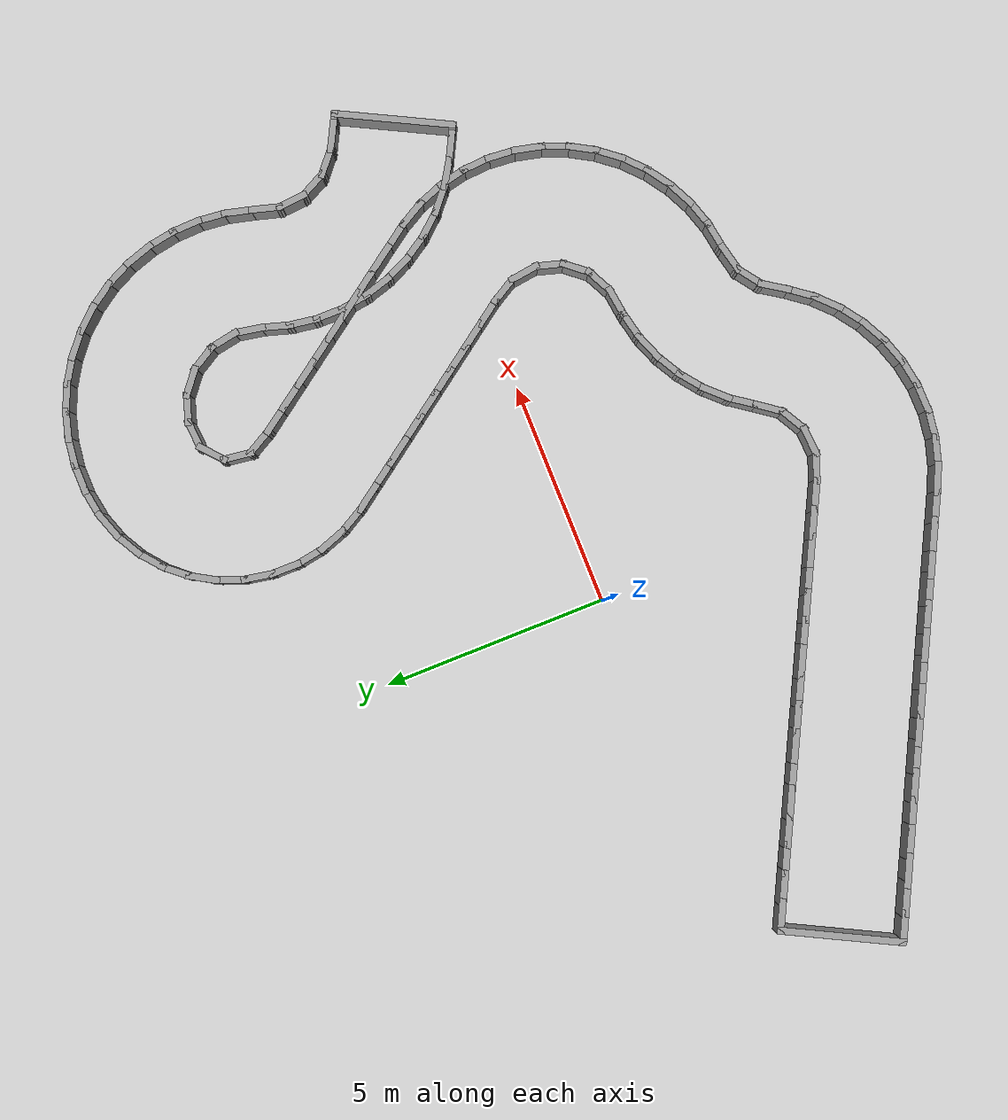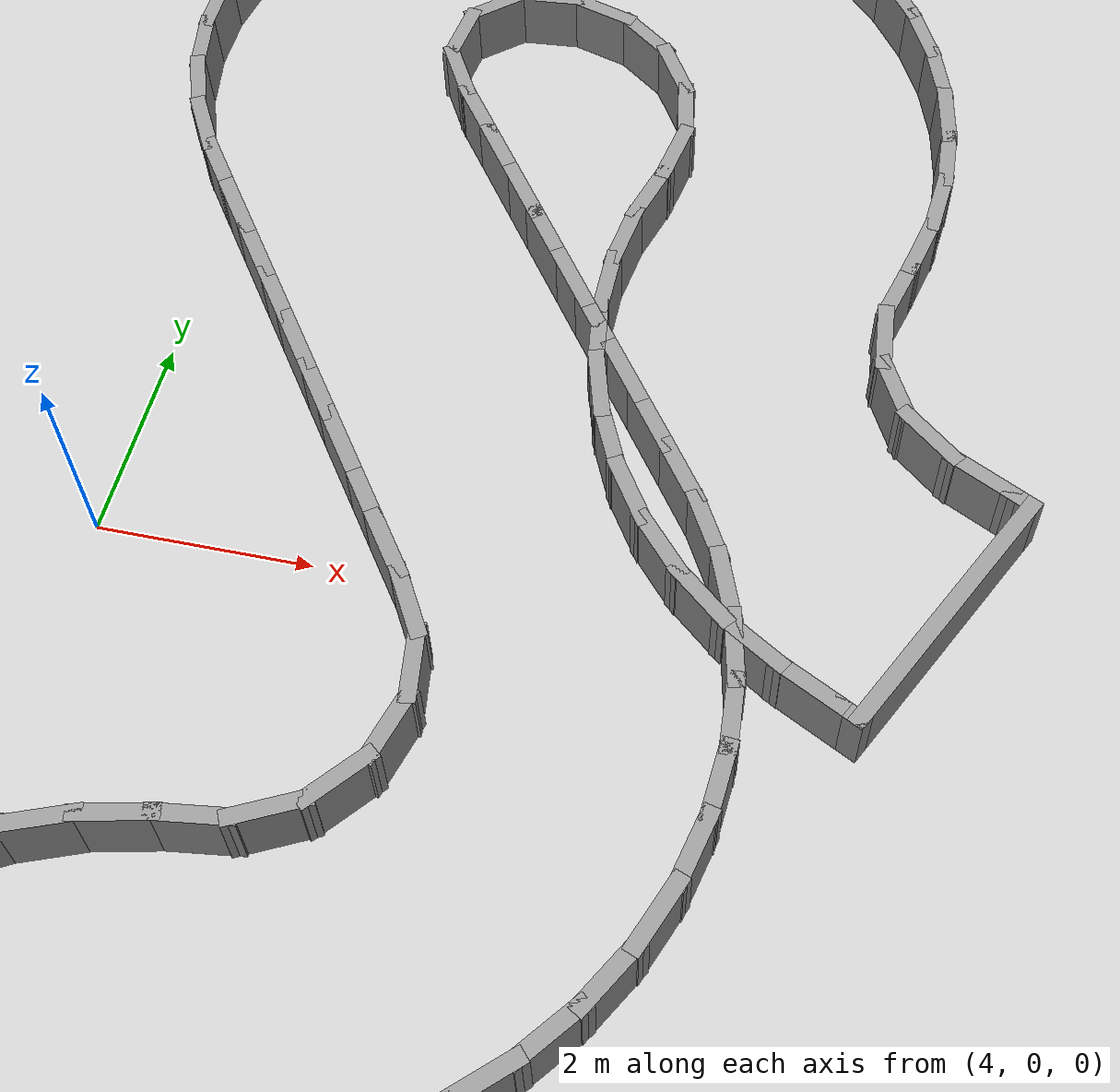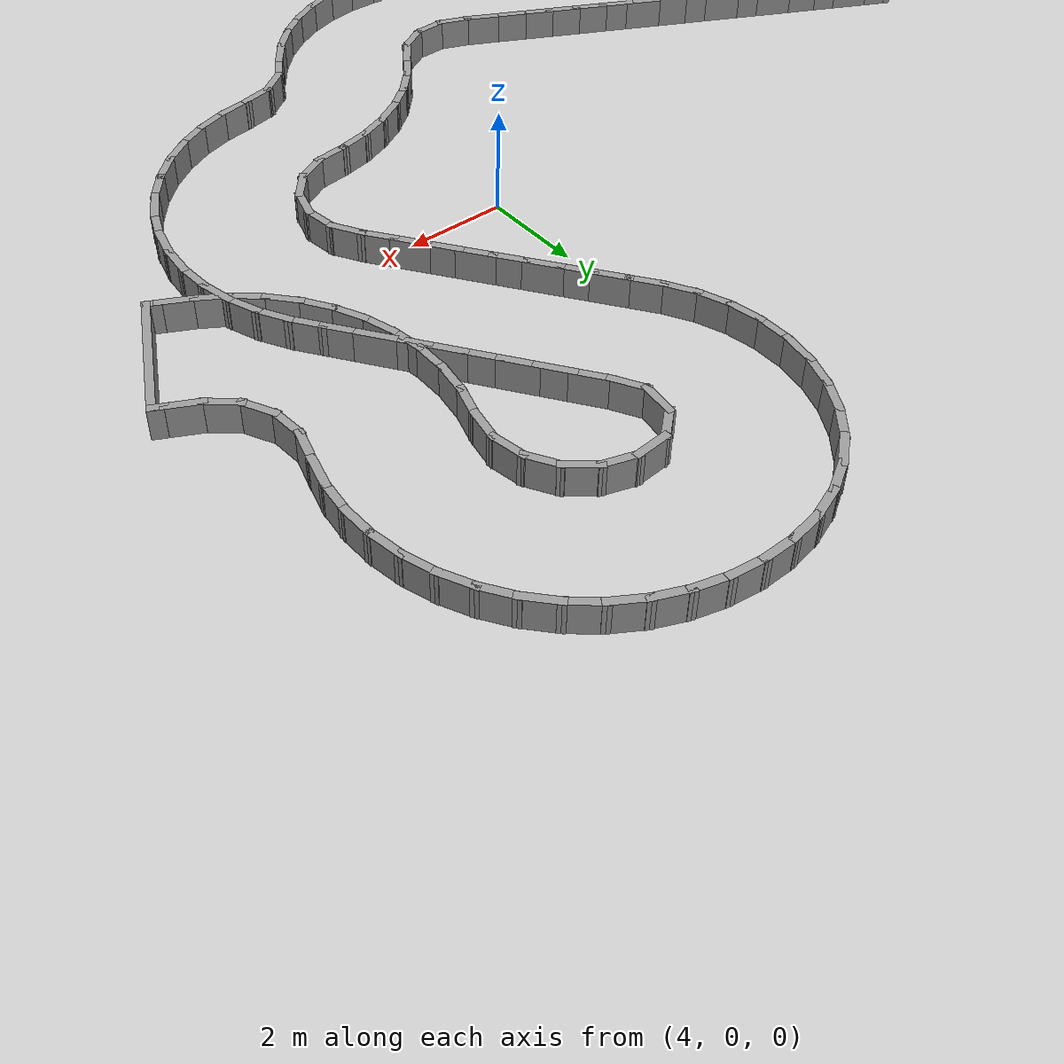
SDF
<?xml version="1.0" ?>
<sdf version='1.7'>
  <world name='default'>
    <plugin name='gazebo_ros_state' filename='libgazebo_ros_state.so'>
      <ros>
        <namespace>/</namespace>
      </ros>
      <update_rate>1000.0</update_rate>
    </plugin>

    <light name='sun' type='directional'>
      <cast_shadows>1</cast_shadows>
      <pose>0 0 10 0 -0 0</pose>
      <diffuse>0.8 0.8 0.8 1</diffuse>
      <specular>0.2 0.2 0.2 1</specular>
      <attenuation>
        <range>1000</range>
        <constant>0.9</constant>
        <linear>0.01</linear>
        <quadratic>0.001</quadratic>
      </attenuation>
      <direction>-0.5 0.1 -0.9</direction>
      <spot>
        <inner_angle>0</inner_angle>
        <outer_angle>0</outer_angle>
        <falloff>0</falloff>
      </spot>
    </light>
    <model name='ground_plane'>
      <static>1</static>
      <link name='link'>
        <collision name='collision'>
          <geometry>
            <plane>
              <normal>0 0 1</normal>
              <size>100 100</size>
            </plane>
          </geometry>
          <surface>
            <friction>
              <ode>
                <mu>100</mu>
                <mu2>50</mu2>
              </ode>
              <torsional>
                <ode/>
              </torsional>
            </friction>
            <contact>
              <ode/>
            </contact>
            <bounce/>
          </surface>
          <max_contacts>10</max_contacts>
        </collision>
        <visual name='visual'>
          <cast_shadows>0</cast_shadows>
          <geometry>
            <plane>
              <normal>0 0 1</normal>
              <size>100 100</size>
            </plane>
          </geometry>
          <material>
            <script>
              <uri>file://media/materials/scripts/gazebo.material</uri>
              <name>Gazebo/Grey</name>
            </script>
          </material>
        </visual>
        <self_collide>0</self_collide>
        <enable_wind>0</enable_wind>
        <kinematic>0</kinematic>
      </link>
    </model>
    <gravity>0 0 -9.8</gravity>
    <magnetic_field>6e-06 2.3e-05 -4.2e-05</magnetic_field>
    <atmosphere type='adiabatic'/>
    <physics type='ode'>
      <max_step_size>0.001</max_step_size>
      <real_time_factor>1</real_time_factor>
      <real_time_update_rate>1000</real_time_update_rate>
    </physics>
    <scene>
      <ambient>0.4 0.4 0.4 1</ambient>
      <background>0.7 0.7 0.7 1</background>
      <shadows>1</shadows>
    </scene>
    <audio>
      <device>default</device>
    </audio>
    <wind/>
    <spherical_coordinates>
      <surface_model>EARTH_WGS84</surface_model>
      <latitude_deg>0</latitude_deg>
      <longitude_deg>0</longitude_deg>
      <elevation>0</elevation>
      <heading_deg>0</heading_deg>
    </spherical_coordinates>
  <model name='rand_turn_02'>
    <pose>0 0 0 0 -0 0</pose>
    <link name='Wall_0'>
      <collision name='Wall_0_Collision'>
        <geometry><box><size>0.7500 0.1500 0.6000</size></box></geometry>
        <pose>0 0 0.3000 0 -0 0</pose>
      </collision>
      <visual name='Wall_0_Visual'>
        <pose>0 0 0.3000 0 -0 0</pose>
        <geometry><box><size>0.7500 0.1500 0.6000</size></box></geometry>
        <material>
          <script>
            <uri>file://media/materials/scripts/gazebo.material</uri>
            <name>Gazebo/Grey</name>
          </script>
          <ambient>1 1 1 1</ambient>
        </material>
      </visual>
      <pose>-7.6089 -1.0157 0 0 -0 -0.46992</pose>
    </link>
    <link name='Wall_1'>
      <collision name='Wall_1_Collision'>
        <geometry><box><size>0.7500 0.1500 0.6000</size></box></geometry>
        <pose>0 0 0.3000 0 -0 0</pose>
      </collision>
      <visual name='Wall_1_Visual'>
        <pose>0 0 0.3000 0 -0 0</pose>
        <geometry><box><size>0.7500 0.1500 0.6000</size></box></geometry>
        <material>
          <script>
            <uri>file://media/materials/scripts/gazebo.material</uri>
            <name>Gazebo/Grey</name>
          </script>
          <ambient>1 1 1 1</ambient>
        </material>
      </visual>
      <pose>-7.0739 -1.2874 0 0 -0 -0.46992</pose>
    </link>
    <link name='Wall_2'>
      <collision name='Wall_2_Collision'>
        <geometry><box><size>0.7500 0.1500 0.6000</size></box></geometry>
        <pose>0 0 0.3000 0 -0 0</pose>
      </collision>
      <visual name='Wall_2_Visual'>
        <pose>0 0 0.3000 0 -0 0</pose>
        <geometry><box><size>0.7500 0.1500 0.6000</size></box></geometry>
        <material>
          <script>
            <uri>file://media/materials/scripts/gazebo.material</uri>
            <name>Gazebo/Grey</name>
          </script>
          <ambient>1 1 1 1</ambient>
        </material>
      </visual>
      <pose>-6.5390 -1.5591 0 0 -0 -0.46992</pose>
    </link>
    <link name='Wall_3'>
      <collision name='Wall_3_Collision'>
        <geometry><box><size>0.7500 0.1500 0.6000</size></box></geometry>
        <pose>0 0 0.3000 0 -0 0</pose>
      </collision>
      <visual name='Wall_3_Visual'>
        <pose>0 0 0.3000 0 -0 0</pose>
        <geometry><box><size>0.7500 0.1500 0.6000</size></box></geometry>
        <material>
          <script>
            <uri>file://media/materials/scripts/gazebo.material</uri>
            <name>Gazebo/Grey</name>
          </script>
          <ambient>1 1 1 1</ambient>
        </material>
      </visual>
      <pose>-6.0040 -1.8308 0 0 -0 -0.46992</pose>
    </link>
    <link name='Wall_4'>
      <collision name='Wall_4_Collision'>
        <geometry><box><size>0.7500 0.1500 0.6000</size></box></geometry>
        <pose>0 0 0.3000 0 -0 0</pose>
      </collision>
      <visual name='Wall_4_Visual'>
        <pose>0 0 0.3000 0 -0 0</pose>
        <geometry><box><size>0.7500 0.1500 0.6000</size></box></geometry>
        <material>
          <script>
            <uri>file://media/materials/scripts/gazebo.material</uri>
            <name>Gazebo/Grey</name>
          </script>
          <ambient>1 1 1 1</ambient>
        </material>
      </visual>
      <pose>-5.4690 -2.1025 0 0 -0 -0.46992</pose>
    </link>
    <link name='Wall_5'>
      <collision name='Wall_5_Collision'>
        <geometry><box><size>0.7500 0.1500 0.6000</size></box></geometry>
        <pose>0 0 0.3000 0 -0 0</pose>
      </collision>
      <visual name='Wall_5_Visual'>
        <pose>0 0 0.3000 0 -0 0</pose>
        <geometry><box><size>0.7500 0.1500 0.6000</size></box></geometry>
        <material>
          <script>
            <uri>file://media/materials/scripts/gazebo.material</uri>
            <name>Gazebo/Grey</name>
          </script>
          <ambient>1 1 1 1</ambient>
        </material>
      </visual>
      <pose>-4.9341 -2.3742 0 0 -0 -0.46992</pose>
    </link>
    <link name='Wall_6'>
      <collision name='Wall_6_Collision'>
        <geometry><box><size>0.7500 0.1500 0.6000</size></box></geometry>
        <pose>0 0 0.3000 0 -0 0</pose>
      </collision>
      <visual name='Wall_6_Visual'>
        <pose>0 0 0.3000 0 -0 0</pose>
        <geometry><box><size>0.7500 0.1500 0.6000</size></box></geometry>
        <material>
          <script>
            <uri>file://media/materials/scripts/gazebo.material</uri>
            <name>Gazebo/Grey</name>
          </script>
          <ambient>1 1 1 1</ambient>
        </material>
      </visual>
      <pose>-4.3991 -2.6458 0 0 -0 -0.46992</pose>
    </link>
    <link name='Wall_7'>
      <collision name='Wall_7_Collision'>
        <geometry><box><size>0.7500 0.1500 0.6000</size></box></geometry>
        <pose>0 0 0.3000 0 -0 0</pose>
      </collision>
      <visual name='Wall_7_Visual'>
        <pose>0 0 0.3000 0 -0 0</pose>
        <geometry><box><size>0.7500 0.1500 0.6000</size></box></geometry>
        <material>
          <script>
            <uri>file://media/materials/scripts/gazebo.material</uri>
            <name>Gazebo/Grey</name>
          </script>
          <ambient>1 1 1 1</ambient>
        </material>
      </visual>
      <pose>-3.8642 -2.9175 0 0 -0 -0.46992</pose>
    </link>
    <link name='Wall_8'>
      <collision name='Wall_8_Collision'>
        <geometry><box><size>0.7500 0.1500 0.6000</size></box></geometry>
        <pose>0 0 0.3000 0 -0 0</pose>
      </collision>
      <visual name='Wall_8_Visual'>
        <pose>0 0 0.3000 0 -0 0</pose>
        <geometry><box><size>0.7500 0.1500 0.6000</size></box></geometry>
        <material>
          <script>
            <uri>file://media/materials/scripts/gazebo.material</uri>
            <name>Gazebo/Grey</name>
          </script>
          <ambient>1 1 1 1</ambient>
        </material>
      </visual>
      <pose>-3.3292 -3.1892 0 0 -0 -0.46992</pose>
    </link>
    <link name='Wall_9'>
      <collision name='Wall_9_Collision'>
        <geometry><box><size>0.7500 0.1500 0.6000</size></box></geometry>
        <pose>0 0 0.3000 0 -0 0</pose>
      </collision>
      <visual name='Wall_9_Visual'>
        <pose>0 0 0.3000 0 -0 0</pose>
        <geometry><box><size>0.7500 0.1500 0.6000</size></box></geometry>
        <material>
          <script>
            <uri>file://media/materials/scripts/gazebo.material</uri>
            <name>Gazebo/Grey</name>
          </script>
          <ambient>1 1 1 1</ambient>
        </material>
      </visual>
      <pose>-2.7942 -3.4609 0 0 -0 -0.46992</pose>
    </link>
    <link name='Wall_10'>
      <collision name='Wall_10_Collision'>
        <geometry><box><size>0.7500 0.1500 0.6000</size></box></geometry>
        <pose>0 0 0.3000 0 -0 0</pose>
      </collision>
      <visual name='Wall_10_Visual'>
        <pose>0 0 0.3000 0 -0 0</pose>
        <geometry><box><size>0.7500 0.1500 0.6000</size></box></geometry>
        <material>
          <script>
            <uri>file://media/materials/scripts/gazebo.material</uri>
            <name>Gazebo/Grey</name>
          </script>
          <ambient>1 1 1 1</ambient>
        </material>
      </visual>
      <pose>-2.2593 -3.7326 0 0 -0 -0.46992</pose>
    </link>
    <link name='Wall_11'>
      <collision name='Wall_11_Collision'>
        <geometry><box><size>0.7500 0.1500 0.6000</size></box></geometry>
        <pose>0 0 0.3000 0 -0 0</pose>
      </collision>
      <visual name='Wall_11_Visual'>
        <pose>0 0 0.3000 0 -0 0</pose>
        <geometry><box><size>0.7500 0.1500 0.6000</size></box></geometry>
        <material>
          <script>
            <uri>file://media/materials/scripts/gazebo.material</uri>
            <name>Gazebo/Grey</name>
          </script>
          <ambient>1 1 1 1</ambient>
        </material>
      </visual>
      <pose>-1.7243 -4.0043 0 0 -0 -0.46992</pose>
    </link>
    <link name='Wall_12'>
      <collision name='Wall_12_Collision'>
        <geometry><box><size>0.7500 0.1500 0.6000</size></box></geometry>
        <pose>0 0 0.3000 0 -0 0</pose>
      </collision>
      <visual name='Wall_12_Visual'>
        <pose>0 0 0.3000 0 -0 0</pose>
        <geometry><box><size>0.7500 0.1500 0.6000</size></box></geometry>
        <material>
          <script>
            <uri>file://media/materials/scripts/gazebo.material</uri>
            <name>Gazebo/Grey</name>
          </script>
          <ambient>1 1 1 1</ambient>
        </material>
      </visual>
      <pose>-1.1893 -4.2760 0 0 -0 -0.46992</pose>
    </link>
    <link name='Wall_13'>
      <collision name='Wall_13_Collision'>
        <geometry><box><size>0.7500 0.1500 0.6000</size></box></geometry>
        <pose>0 0 0.3000 0 -0 0</pose>
      </collision>
      <visual name='Wall_13_Visual'>
        <pose>0 0 0.3000 0 -0 0</pose>
        <geometry><box><size>0.7500 0.1500 0.6000</size></box></geometry>
        <material>
          <script>
            <uri>file://media/materials/scripts/gazebo.material</uri>
            <name>Gazebo/Grey</name>
          </script>
          <ambient>1 1 1 1</ambient>
        </material>
      </visual>
      <pose>-0.6544 -4.5476 0 0 -0 -0.46992</pose>
    </link>
    <link name='Wall_14'>
      <collision name='Wall_14_Collision'>
        <geometry><box><size>0.7500 0.1500 0.6000</size></box></geometry>
        <pose>0 0 0.3000 0 -0 0</pose>
      </collision>
      <visual name='Wall_14_Visual'>
        <pose>0 0 0.3000 0 -0 0</pose>
        <geometry><box><size>0.7500 0.1500 0.6000</size></box></geometry>
        <material>
          <script>
            <uri>file://media/materials/scripts/gazebo.material</uri>
            <name>Gazebo/Grey</name>
          </script>
          <ambient>1 1 1 1</ambient>
        </material>
      </visual>
      <pose>-0.1194 -4.8193 0 0 -0 -0.46992</pose>
    </link>
    <link name='Wall_15'>
      <collision name='Wall_15_Collision'>
        <geometry><box><size>0.7500 0.1500 0.6000</size></box></geometry>
        <pose>0 0 0.3000 0 -0 0</pose>
      </collision>
      <visual name='Wall_15_Visual'>
        <pose>0 0 0.3000 0 -0 0</pose>
        <geometry><box><size>0.7500 0.1500 0.6000</size></box></geometry>
        <material>
          <script>
            <uri>file://media/materials/scripts/gazebo.material</uri>
            <name>Gazebo/Grey</name>
          </script>
          <ambient>1 1 1 1</ambient>
        </material>
      </visual>
      <pose>0.4156 -5.0910 0 0 -0 -0.46992</pose>
    </link>
    <link name='Wall_16'>
      <collision name='Wall_16_Collision'>
        <geometry><box><size>0.7470 0.1500 0.6000</size></box></geometry>
        <pose>0 0 0.3000 0 -0 0</pose>
      </collision>
      <visual name='Wall_16_Visual'>
        <pose>0 0 0.3000 0 -0 0</pose>
        <geometry><box><size>0.7470 0.1500 0.6000</size></box></geometry>
        <material>
          <script>
            <uri>file://media/materials/scripts/gazebo.material</uri>
            <name>Gazebo/Grey</name>
          </script>
          <ambient>1 1 1 1</ambient>
        </material>
      </visual>
      <pose>0.9614 -5.3347 0 0 -0 -0.36971</pose>
    </link>
    <link name='Wall_17'>
      <collision name='Wall_17_Collision'>
        <geometry><box><size>0.7449 0.1500 0.6000</size></box></geometry>
        <pose>0 0 0.3000 0 -0 0</pose>
      </collision>
      <visual name='Wall_17_Visual'>
        <pose>0 0 0.3000 0 -0 0</pose>
        <geometry><box><size>0.7449 0.1500 0.6000</size></box></geometry>
        <material>
          <script>
            <uri>file://media/materials/scripts/gazebo.material</uri>
            <name>Gazebo/Grey</name>
          </script>
          <ambient>1 1 1 1</ambient>
        </material>
      </visual>
      <pose>1.5367 -5.4259 0 0 -0 0.05612</pose>
    </link>
    <link name='Wall_18'>
      <collision name='Wall_18_Collision'>
        <geometry><box><size>0.7449 0.1500 0.6000</size></box></geometry>
        <pose>0 0 0.3000 0 -0 0</pose>
      </collision>
      <visual name='Wall_18_Visual'>
        <pose>0 0 0.3000 0 -0 0</pose>
        <geometry><box><size>0.7449 0.1500 0.6000</size></box></geometry>
        <material>
          <script>
            <uri>file://media/materials/scripts/gazebo.material</uri>
            <name>Gazebo/Grey</name>
          </script>
          <ambient>1 1 1 1</ambient>
        </material>
      </visual>
      <pose>2.0937 -5.2648 0 0 -0 0.50683</pose>
    </link>
    <link name='Wall_19'>
      <collision name='Wall_19_Collision'>
        <geometry><box><size>0.7466 0.1500 0.6000</size></box></geometry>
        <pose>0 0 0.3000 0 -0 0</pose>
      </collision>
      <visual name='Wall_19_Visual'>
        <pose>0 0 0.3000 0 -0 0</pose>
        <geometry><box><size>0.7466 0.1500 0.6000</size></box></geometry>
        <material>
          <script>
            <uri>file://media/materials/scripts/gazebo.material</uri>
            <name>Gazebo/Grey</name>
          </script>
          <ambient>1 1 1 1</ambient>
        </material>
      </visual>
      <pose>2.5302 -4.8800 0 0 -0 0.93785</pose>
    </link>
    <link name='Wall_20'>
      <collision name='Wall_20_Collision'>
        <geometry><box><size>0.7494 0.1500 0.6000</size></box></geometry>
        <pose>0 0 0.3000 0 -0 0</pose>
      </collision>
      <visual name='Wall_20_Visual'>
        <pose>0 0 0.3000 0 -0 0</pose>
        <geometry><box><size>0.7494 0.1500 0.6000</size></box></geometry>
        <material>
          <script>
            <uri>file://media/materials/scripts/gazebo.material</uri>
            <name>Gazebo/Grey</name>
          </script>
          <ambient>1 1 1 1</ambient>
        </material>
      </visual>
      <pose>2.8796 -4.3946 0 0 -0 0.95586</pose>
    </link>
    <link name='Wall_21'>
      <collision name='Wall_21_Collision'>
        <geometry><box><size>0.7494 0.1500 0.6000</size></box></geometry>
        <pose>0 0 0.3000 0 -0 0</pose>
      </collision>
      <visual name='Wall_21_Visual'>
        <pose>0 0 0.3000 0 -0 0</pose>
        <geometry><box><size>0.7494 0.1500 0.6000</size></box></geometry>
        <material>
          <script>
            <uri>file://media/materials/scripts/gazebo.material</uri>
            <name>Gazebo/Grey</name>
          </script>
          <ambient>1 1 1 1</ambient>
        </material>
      </visual>
      <pose>3.2594 -3.9330 0 0 -0 0.80891</pose>
    </link>
    <link name='Wall_22'>
      <collision name='Wall_22_Collision'>
        <geometry><box><size>0.7494 0.1500 0.6000</size></box></geometry>
        <pose>0 0 0.3000 0 -0 0</pose>
      </collision>
      <visual name='Wall_22_Visual'>
        <pose>0 0 0.3000 0 -0 0</pose>
        <geometry><box><size>0.7494 0.1500 0.6000</size></box></geometry>
        <material>
          <script>
            <uri>file://media/materials/scripts/gazebo.material</uri>
            <name>Gazebo/Grey</name>
          </script>
          <ambient>1 1 1 1</ambient>
        </material>
      </visual>
      <pose>3.7027 -3.5319 0 0 -0 0.66195</pose>
    </link>
    <link name='Wall_23'>
      <collision name='Wall_23_Collision'>
        <geometry><box><size>0.7494 0.1500 0.6000</size></box></geometry>
        <pose>0 0 0.3000 0 -0 0</pose>
      </collision>
      <visual name='Wall_23_Visual'>
        <pose>0 0 0.3000 0 -0 0</pose>
        <geometry><box><size>0.7494 0.1500 0.6000</size></box></geometry>
        <material>
          <script>
            <uri>file://media/materials/scripts/gazebo.material</uri>
            <name>Gazebo/Grey</name>
          </script>
          <ambient>1 1 1 1</ambient>
        </material>
      </visual>
      <pose>4.1999 -3.2001 0 0 -0 0.51500</pose>
    </link>
    <link name='Wall_24'>
      <collision name='Wall_24_Collision'>
        <geometry><box><size>0.7495 0.1500 0.6000</size></box></geometry>
        <pose>0 0 0.3000 0 -0 0</pose>
      </collision>
      <visual name='Wall_24_Visual'>
        <pose>0 0 0.3000 0 -0 0</pose>
        <geometry><box><size>0.7495 0.1500 0.6000</size></box></geometry>
        <material>
          <script>
            <uri>file://media/materials/scripts/gazebo.material</uri>
            <name>Gazebo/Grey</name>
          </script>
          <ambient>1 1 1 1</ambient>
        </material>
      </visual>
      <pose>4.7404 -2.9446 0 0 -0 0.36805</pose>
    </link>
    <link name='Wall_25'>
      <collision name='Wall_25_Collision'>
        <geometry><box><size>0.7495 0.1500 0.6000</size></box></geometry>
        <pose>0 0 0.3000 0 -0 0</pose>
      </collision>
      <visual name='Wall_25_Visual'>
        <pose>0 0 0.3000 0 -0 0</pose>
        <geometry><box><size>0.7495 0.1500 0.6000</size></box></geometry>
        <material>
          <script>
            <uri>file://media/materials/scripts/gazebo.material</uri>
            <name>Gazebo/Grey</name>
          </script>
          <ambient>1 1 1 1</ambient>
        </material>
      </visual>
      <pose>5.3125 -2.7712 0 0 -0 0.22072</pose>
    </link>
    <link name='Wall_26'>
      <collision name='Wall_26_Collision'>
        <geometry><box><size>0.7493 0.1500 0.6000</size></box></geometry>
        <pose>0 0 0.3000 0 -0 0</pose>
      </collision>
      <visual name='Wall_26_Visual'>
        <pose>0 0 0.3000 0 -0 0</pose>
        <geometry><box><size>0.7493 0.1500 0.6000</size></box></geometry>
        <material>
          <script>
            <uri>file://media/materials/scripts/gazebo.material</uri>
            <name>Gazebo/Grey</name>
          </script>
          <ambient>1 1 1 1</ambient>
        </material>
      </visual>
      <pose>5.9020 -2.6663 0 0 -0 0.13148</pose>
    </link>
    <link name='Wall_27'>
      <collision name='Wall_27_Collision'>
        <geometry><box><size>0.7457 0.1500 0.6000</size></box></geometry>
        <pose>0 0 0.3000 0 -0 0</pose>
      </collision>
      <visual name='Wall_27_Visual'>
        <pose>0 0 0.3000 0 -0 0</pose>
        <geometry><box><size>0.7457 0.1500 0.6000</size></box></geometry>
        <material>
          <script>
            <uri>file://media/materials/scripts/gazebo.material</uri>
            <name>Gazebo/Grey</name>
          </script>
          <ambient>1 1 1 1</ambient>
        </material>
      </visual>
      <pose>6.4657 -2.4941 0 0 -0 0.46226</pose>
    </link>
    <link name='Wall_28'>
      <collision name='Wall_28_Collision'>
        <geometry><box><size>0.7457 0.1500 0.6000</size></box></geometry>
        <pose>0 0 0.3000 0 -0 0</pose>
      </collision>
      <visual name='Wall_28_Visual'>
        <pose>0 0 0.3000 0 -0 0</pose>
        <geometry><box><size>0.7457 0.1500 0.6000</size></box></geometry>
        <material>
          <script>
            <uri>file://media/materials/scripts/gazebo.material</uri>
            <name>Gazebo/Grey</name>
          </script>
          <ambient>1 1 1 1</ambient>
        </material>
      </visual>
      <pose>6.9225 -2.1322 0 0 -0 0.87773</pose>
    </link>
    <link name='Wall_29'>
      <collision name='Wall_29_Collision'>
        <geometry><box><size>0.7457 0.1500 0.6000</size></box></geometry>
        <pose>0 0 0.3000 0 -0 0</pose>
      </collision>
      <visual name='Wall_29_Visual'>
        <pose>0 0 0.3000 0 -0 0</pose>
        <geometry><box><size>0.7457 0.1500 0.6000</size></box></geometry>
        <material>
          <script>
            <uri>file://media/materials/scripts/gazebo.material</uri>
            <name>Gazebo/Grey</name>
          </script>
          <ambient>1 1 1 1</ambient>
        </material>
      </visual>
      <pose>7.1945 -1.6167 0 0 -0 1.29283</pose>
    </link>
    <link name='Wall_30'>
      <collision name='Wall_30_Collision'>
        <geometry><box><size>0.7457 0.1500 0.6000</size></box></geometry>
        <pose>0 0 0.3000 0 -0 0</pose>
      </collision>
      <visual name='Wall_30_Visual'>
        <pose>0 0 0.3000 0 -0 0</pose>
        <geometry><box><size>0.7457 0.1500 0.6000</size></box></geometry>
        <material>
          <script>
            <uri>file://media/materials/scripts/gazebo.material</uri>
            <name>Gazebo/Grey</name>
          </script>
          <ambient>1 1 1 1</ambient>
        </material>
      </visual>
      <pose>7.2356 -1.0352 0 0 -0 1.70773</pose>
    </link>
    <link name='Wall_31'>
      <collision name='Wall_31_Collision'>
        <geometry><box><size>0.7473 0.1500 0.6000</size></box></geometry>
        <pose>0 0 0.3000 0 -0 0</pose>
      </collision>
      <visual name='Wall_31_Visual'>
        <pose>0 0 0.3000 0 -0 0</pose>
        <geometry><box><size>0.7473 0.1500 0.6000</size></box></geometry>
        <material>
          <script>
            <uri>file://media/materials/scripts/gazebo.material</uri>
            <name>Gazebo/Grey</name>
          </script>
          <ambient>1 1 1 1</ambient>
        </material>
      </visual>
      <pose>7.0434 -0.4829 0 0 -0 2.10306</pose>
    </link>
    <link name='Wall_32'>
      <collision name='Wall_32_Collision'>
        <geometry><box><size>0.7500 0.1500 0.6000</size></box></geometry>
        <pose>0 0 0.3000 0 -0 0</pose>
      </collision>
      <visual name='Wall_32_Visual'>
        <pose>0 0 0.3000 0 -0 0</pose>
        <geometry><box><size>0.7500 0.1500 0.6000</size></box></geometry>
        <material>
          <script>
            <uri>file://media/materials/scripts/gazebo.material</uri>
            <name>Gazebo/Grey</name>
          </script>
          <ambient>1 1 1 1</ambient>
        </material>
      </visual>
      <pose>6.7163 0.0177 0 0 -0 2.19589</pose>
    </link>
    <link name='Wall_33'>
      <collision name='Wall_33_Collision'>
        <geometry><box><size>0.7500 0.1500 0.6000</size></box></geometry>
        <pose>0 0 0.3000 0 -0 0</pose>
      </collision>
      <visual name='Wall_33_Visual'>
        <pose>0 0 0.3000 0 -0 0</pose>
        <geometry><box><size>0.7500 0.1500 0.6000</size></box></geometry>
        <material>
          <script>
            <uri>file://media/materials/scripts/gazebo.material</uri>
            <name>Gazebo/Grey</name>
          </script>
          <ambient>1 1 1 1</ambient>
        </material>
      </visual>
      <pose>6.3652 0.5043 0 0 -0 2.19589</pose>
    </link>
    <link name='Wall_34'>
      <collision name='Wall_34_Collision'>
        <geometry><box><size>0.7500 0.1500 0.6000</size></box></geometry>
        <pose>0 0 0.3000 0 -0 0</pose>
      </collision>
      <visual name='Wall_34_Visual'>
        <pose>0 0 0.3000 0 -0 0</pose>
        <geometry><box><size>0.7500 0.1500 0.6000</size></box></geometry>
        <material>
          <script>
            <uri>file://media/materials/scripts/gazebo.material</uri>
            <name>Gazebo/Grey</name>
          </script>
          <ambient>1 1 1 1</ambient>
        </material>
      </visual>
      <pose>6.0141 0.9908 0 0 -0 2.19589</pose>
    </link>
    <link name='Wall_35'>
      <collision name='Wall_35_Collision'>
        <geometry><box><size>0.7500 0.1500 0.6000</size></box></geometry>
        <pose>0 0 0.3000 0 -0 0</pose>
      </collision>
      <visual name='Wall_35_Visual'>
        <pose>0 0 0.3000 0 -0 0</pose>
        <geometry><box><size>0.7500 0.1500 0.6000</size></box></geometry>
        <material>
          <script>
            <uri>file://media/materials/scripts/gazebo.material</uri>
            <name>Gazebo/Grey</name>
          </script>
          <ambient>1 1 1 1</ambient>
        </material>
      </visual>
      <pose>5.6630 1.4774 0 0 -0 2.19589</pose>
    </link>
    <link name='Wall_36'>
      <collision name='Wall_36_Collision'>
        <geometry><box><size>0.7500 0.1500 0.6000</size></box></geometry>
        <pose>0 0 0.3000 0 -0 0</pose>
      </collision>
      <visual name='Wall_36_Visual'>
        <pose>0 0 0.3000 0 -0 0</pose>
        <geometry><box><size>0.7500 0.1500 0.6000</size></box></geometry>
        <material>
          <script>
            <uri>file://media/materials/scripts/gazebo.material</uri>
            <name>Gazebo/Grey</name>
          </script>
          <ambient>1 1 1 1</ambient>
        </material>
      </visual>
      <pose>5.3119 1.9639 0 0 -0 2.19589</pose>
    </link>
    <link name='Wall_37'>
      <collision name='Wall_37_Collision'>
        <geometry><box><size>0.7500 0.1500 0.6000</size></box></geometry>
        <pose>0 0 0.3000 0 -0 0</pose>
      </collision>
      <visual name='Wall_37_Visual'>
        <pose>0 0 0.3000 0 -0 0</pose>
        <geometry><box><size>0.7500 0.1500 0.6000</size></box></geometry>
        <material>
          <script>
            <uri>file://media/materials/scripts/gazebo.material</uri>
            <name>Gazebo/Grey</name>
          </script>
          <ambient>1 1 1 1</ambient>
        </material>
      </visual>
      <pose>4.9608 2.4505 0 0 -0 2.19589</pose>
    </link>
    <link name='Wall_38'>
      <collision name='Wall_38_Collision'>
        <geometry><box><size>0.7500 0.1500 0.6000</size></box></geometry>
        <pose>0 0 0.3000 0 -0 0</pose>
      </collision>
      <visual name='Wall_38_Visual'>
        <pose>0 0 0.3000 0 -0 0</pose>
        <geometry><box><size>0.7500 0.1500 0.6000</size></box></geometry>
        <material>
          <script>
            <uri>file://media/materials/scripts/gazebo.material</uri>
            <name>Gazebo/Grey</name>
          </script>
          <ambient>1 1 1 1</ambient>
        </material>
      </visual>
      <pose>4.6097 2.9370 0 0 -0 2.19589</pose>
    </link>
    <link name='Wall_39'>
      <collision name='Wall_39_Collision'>
        <geometry><box><size>0.7500 0.1500 0.6000</size></box></geometry>
        <pose>0 0 0.3000 0 -0 0</pose>
      </collision>
      <visual name='Wall_39_Visual'>
        <pose>0 0 0.3000 0 -0 0</pose>
        <geometry><box><size>0.7500 0.1500 0.6000</size></box></geometry>
        <material>
          <script>
            <uri>file://media/materials/scripts/gazebo.material</uri>
            <name>Gazebo/Grey</name>
          </script>
          <ambient>1 1 1 1</ambient>
        </material>
      </visual>
      <pose>4.2586 3.4236 0 0 -0 2.19589</pose>
    </link>
    <link name='Wall_40'>
      <collision name='Wall_40_Collision'>
        <geometry><box><size>0.7500 0.1500 0.6000</size></box></geometry>
        <pose>0 0 0.3000 0 -0 0</pose>
      </collision>
      <visual name='Wall_40_Visual'>
        <pose>0 0 0.3000 0 -0 0</pose>
        <geometry><box><size>0.7500 0.1500 0.6000</size></box></geometry>
        <material>
          <script>
            <uri>file://media/materials/scripts/gazebo.material</uri>
            <name>Gazebo/Grey</name>
          </script>
          <ambient>1 1 1 1</ambient>
        </material>
      </visual>
      <pose>3.9081 3.9105 0 0 -0 2.19328</pose>
    </link>
    <link name='Wall_41'>
      <collision name='Wall_41_Collision'>
        <geometry><box><size>0.7492 0.1500 0.6000</size></box></geometry>
        <pose>0 0 0.3000 0 -0 0</pose>
      </collision>
      <visual name='Wall_41_Visual'>
        <pose>0 0 0.3000 0 -0 0</pose>
        <geometry><box><size>0.7492 0.1500 0.6000</size></box></geometry>
        <material>
          <script>
            <uri>file://media/materials/scripts/gazebo.material</uri>
            <name>Gazebo/Grey</name>
          </script>
          <ambient>1 1 1 1</ambient>
        </material>
      </visual>
      <pose>3.5852 4.4147 0 0 -0 2.08748</pose>
    </link>
    <link name='Wall_42'>
      <collision name='Wall_42_Collision'>
        <geometry><box><size>0.7492 0.1500 0.6000</size></box></geometry>
        <pose>0 0 0.3000 0 -0 0</pose>
      </collision>
      <visual name='Wall_42_Visual'>
        <pose>0 0 0.3000 0 -0 0</pose>
        <geometry><box><size>0.7492 0.1500 0.6000</size></box></geometry>
        <material>
          <script>
            <uri>file://media/materials/scripts/gazebo.material</uri>
            <name>Gazebo/Grey</name>
          </script>
          <ambient>1 1 1 1</ambient>
        </material>
      </visual>
      <pose>3.3367 4.9575 0 0 -0 1.91292</pose>
    </link>
    <link name='Wall_43'>
      <collision name='Wall_43_Collision'>
        <geometry><box><size>0.7492 0.1500 0.6000</size></box></geometry>
        <pose>0 0 0.3000 0 -0 0</pose>
      </collision>
      <visual name='Wall_43_Visual'>
        <pose>0 0 0.3000 0 -0 0</pose>
        <geometry><box><size>0.7492 0.1500 0.6000</size></box></geometry>
        <material>
          <script>
            <uri>file://media/materials/scripts/gazebo.material</uri>
            <name>Gazebo/Grey</name>
          </script>
          <ambient>1 1 1 1</ambient>
        </material>
      </visual>
      <pose>3.1866 5.5352 0 0 -0 1.73694</pose>
    </link>
    <link name='Wall_44'>
      <collision name='Wall_44_Collision'>
        <geometry><box><size>0.7491 0.1500 0.6000</size></box></geometry>
        <pose>0 0 0.3000 0 -0 0</pose>
      </collision>
      <visual name='Wall_44_Visual'>
        <pose>0 0 0.3000 0 -0 0</pose>
        <geometry><box><size>0.7491 0.1500 0.6000</size></box></geometry>
        <material>
          <script>
            <uri>file://media/materials/scripts/gazebo.material</uri>
            <name>Gazebo/Grey</name>
          </script>
          <ambient>1 1 1 1</ambient>
        </material>
      </visual>
      <pose>3.1393 6.1302 0 0 -0 1.56327</pose>
    </link>
    <link name='Wall_45'>
      <collision name='Wall_45_Collision'>
        <geometry><box><size>0.7492 0.1500 0.6000</size></box></geometry>
        <pose>0 0 0.3000 0 -0 0</pose>
      </collision>
      <visual name='Wall_45_Visual'>
        <pose>0 0 0.3000 0 -0 0</pose>
        <geometry><box><size>0.7492 0.1500 0.6000</size></box></geometry>
        <material>
          <script>
            <uri>file://media/materials/scripts/gazebo.material</uri>
            <name>Gazebo/Grey</name>
          </script>
          <ambient>1 1 1 1</ambient>
        </material>
      </visual>
      <pose>3.1956 6.7245 0 0 -0 1.38959</pose>
    </link>
    <link name='Wall_46'>
      <collision name='Wall_46_Collision'>
        <geometry><box><size>0.7492 0.1500 0.6000</size></box></geometry>
        <pose>0 0 0.3000 0 -0 0</pose>
      </collision>
      <visual name='Wall_46_Visual'>
        <pose>0 0 0.3000 0 -0 0</pose>
        <geometry><box><size>0.7492 0.1500 0.6000</size></box></geometry>
        <material>
          <script>
            <uri>file://media/materials/scripts/gazebo.material</uri>
            <name>Gazebo/Grey</name>
          </script>
          <ambient>1 1 1 1</ambient>
        </material>
      </visual>
      <pose>3.3543 7.2999 0 0 -0 1.21352</pose>
    </link>
    <link name='Wall_47'>
      <collision name='Wall_47_Collision'>
        <geometry><box><size>0.7492 0.1500 0.6000</size></box></geometry>
        <pose>0 0 0.3000 0 -0 0</pose>
      </collision>
      <visual name='Wall_47_Visual'>
        <pose>0 0 0.3000 0 -0 0</pose>
        <geometry><box><size>0.7492 0.1500 0.6000</size></box></geometry>
        <material>
          <script>
            <uri>file://media/materials/scripts/gazebo.material</uri>
            <name>Gazebo/Grey</name>
          </script>
          <ambient>1 1 1 1</ambient>
        </material>
      </visual>
      <pose>3.6111 7.8387 0 0 -0 1.03878</pose>
    </link>
    <link name='Wall_48'>
      <collision name='Wall_48_Collision'>
        <geometry><box><size>0.7491 0.1500 0.6000</size></box></geometry>
        <pose>0 0 0.3000 0 -0 0</pose>
      </collision>
      <visual name='Wall_48_Visual'>
        <pose>0 0 0.3000 0 -0 0</pose>
        <geometry><box><size>0.7491 0.1500 0.6000</size></box></geometry>
        <material>
          <script>
            <uri>file://media/materials/scripts/gazebo.material</uri>
            <name>Gazebo/Grey</name>
          </script>
          <ambient>1 1 1 1</ambient>
        </material>
      </visual>
      <pose>3.9573 8.3249 0 0 -0 0.86510</pose>
    </link>
    <link name='Wall_49'>
      <collision name='Wall_49_Collision'>
        <geometry><box><size>0.7492 0.1500 0.6000</size></box></geometry>
        <pose>0 0 0.3000 0 -0 0</pose>
      </collision>
      <visual name='Wall_49_Visual'>
        <pose>0 0 0.3000 0 -0 0</pose>
        <geometry><box><size>0.7492 0.1500 0.6000</size></box></geometry>
        <material>
          <script>
            <uri>file://media/materials/scripts/gazebo.material</uri>
            <name>Gazebo/Grey</name>
          </script>
          <ambient>1 1 1 1</ambient>
        </material>
      </visual>
      <pose>4.3825 8.7439 0 0 -0 0.69125</pose>
    </link>
    <link name='Wall_50'>
      <collision name='Wall_50_Collision'>
        <geometry><box><size>0.7492 0.1500 0.6000</size></box></geometry>
        <pose>0 0 0.3000 0 -0 0</pose>
      </collision>
      <visual name='Wall_50_Visual'>
        <pose>0 0 0.3000 0 -0 0</pose>
        <geometry><box><size>0.7492 0.1500 0.6000</size></box></geometry>
        <material>
          <script>
            <uri>file://media/materials/scripts/gazebo.material</uri>
            <name>Gazebo/Grey</name>
          </script>
          <ambient>1 1 1 1</ambient>
        </material>
      </visual>
      <pose>4.8742 9.0823 0 0 -0 0.51429</pose>
    </link>
    <link name='Wall_51'>
      <collision name='Wall_51_Collision'>
        <geometry><box><size>0.7491 0.1500 0.6000</size></box></geometry>
        <pose>0 0 0.3000 0 -0 0</pose>
      </collision>
      <visual name='Wall_51_Visual'>
        <pose>0 0 0.3000 0 -0 0</pose>
        <geometry><box><size>0.7491 0.1500 0.6000</size></box></geometry>
        <material>
          <script>
            <uri>file://media/materials/scripts/gazebo.material</uri>
            <name>Gazebo/Grey</name>
          </script>
          <ambient>1 1 1 1</ambient>
        </material>
      </visual>
      <pose>5.4174 9.3298 0 0 -0 0.34062</pose>
    </link>
    <link name='Wall_52'>
      <collision name='Wall_52_Collision'>
        <geometry><box><size>0.7492 0.1500 0.6000</size></box></geometry>
        <pose>0 0 0.3000 0 -0 0</pose>
      </collision>
      <visual name='Wall_52_Visual'>
        <pose>0 0 0.3000 0 -0 0</pose>
        <geometry><box><size>0.7492 0.1500 0.6000</size></box></geometry>
        <material>
          <script>
            <uri>file://media/materials/scripts/gazebo.material</uri>
            <name>Gazebo/Grey</name>
          </script>
          <ambient>1 1 1 1</ambient>
        </material>
      </visual>
      <pose>5.9951 9.4799 0 0 -0 0.16792</pose>
    </link>
    <link name='Wall_53'>
      <collision name='Wall_53_Collision'>
        <geometry><box><size>0.7495 0.1500 0.6000</size></box></geometry>
        <pose>0 0 0.3000 0 -0 0</pose>
      </collision>
      <visual name='Wall_53_Visual'>
        <pose>0 0 0.3000 0 -0 0</pose>
        <geometry><box><size>0.7495 0.1500 0.6000</size></box></geometry>
        <material>
          <script>
            <uri>file://media/materials/scripts/gazebo.material</uri>
            <name>Gazebo/Grey</name>
          </script>
          <ambient>1 1 1 1</ambient>
        </material>
      </visual>
      <pose>6.5902 9.5350 0 0 -0 0.01663</pose>
    </link>
    <link name='Wall_54'>
      <collision name='Wall_54_Collision'>
        <geometry><box><size>0.7495 0.1500 0.6000</size></box></geometry>
        <pose>0 0 0.3000 0 -0 0</pose>
      </collision>
      <visual name='Wall_54_Visual'>
        <pose>0 0 0.3000 0 -0 0</pose>
        <geometry><box><size>0.7495 0.1500 0.6000</size></box></geometry>
        <material>
          <script>
            <uri>file://media/materials/scripts/gazebo.material</uri>
            <name>Gazebo/Grey</name>
          </script>
          <ambient>1 1 1 1</ambient>
        </material>
      </visual>
      <pose>7.1873 9.5030 0 0 -0 -0.12383</pose>
    </link>
    <link name='Wall_55'>
      <collision name='Wall_55_Collision'>
        <geometry><box><size>0.7495 0.1500 0.6000</size></box></geometry>
        <pose>0 0 0.3000 0 -0 0</pose>
      </collision>
      <visual name='Wall_55_Visual'>
        <pose>0 0 0.3000 0 -0 0</pose>
        <geometry><box><size>0.7495 0.1500 0.6000</size></box></geometry>
        <material>
          <script>
            <uri>file://media/materials/scripts/gazebo.material</uri>
            <name>Gazebo/Grey</name>
          </script>
          <ambient>1 1 1 1</ambient>
        </material>
      </visual>
      <pose>7.7741 9.3876 0 0 -0 -0.26429</pose>
    </link>
    <link name='Wall_56'>
      <collision name='Wall_56_Collision'>
        <geometry><box><size>0.7495 0.1500 0.6000</size></box></geometry>
        <pose>0 0 0.3000 0 -0 0</pose>
      </collision>
      <visual name='Wall_56_Visual'>
        <pose>0 0 0.3000 0 -0 0</pose>
        <geometry><box><size>0.7495 0.1500 0.6000</size></box></geometry>
        <material>
          <script>
            <uri>file://media/materials/scripts/gazebo.material</uri>
            <name>Gazebo/Grey</name>
          </script>
          <ambient>1 1 1 1</ambient>
        </material>
      </visual>
      <pose>8.3389 9.1913 0 0 -0 -0.40475</pose>
    </link>
    <link name='Wall_57'>
      <collision name='Wall_57_Collision'>
        <geometry><box><size>0.7495 0.1500 0.6000</size></box></geometry>
        <pose>0 0 0.3000 0 -0 0</pose>
      </collision>
      <visual name='Wall_57_Visual'>
        <pose>0 0 0.3000 0 -0 0</pose>
        <geometry><box><size>0.7495 0.1500 0.6000</size></box></geometry>
        <material>
          <script>
            <uri>file://media/materials/scripts/gazebo.material</uri>
            <name>Gazebo/Grey</name>
          </script>
          <ambient>1 1 1 1</ambient>
        </material>
      </visual>
      <pose>8.8706 8.9176 0 0 -0 -0.54607</pose>
    </link>
    <link name='Wall_58'>
      <collision name='Wall_58_Collision'>
        <geometry><box><size>0.7495 0.1500 0.6000</size></box></geometry>
        <pose>0 0 0.3000 0 -0 0</pose>
      </collision>
      <visual name='Wall_58_Visual'>
        <pose>0 0 0.3000 0 -0 0</pose>
        <geometry><box><size>0.7495 0.1500 0.6000</size></box></geometry>
        <material>
          <script>
            <uri>file://media/materials/scripts/gazebo.material</uri>
            <name>Gazebo/Grey</name>
          </script>
          <ambient>1 1 1 1</ambient>
        </material>
      </visual>
      <pose>9.3585 8.5718 0 0 -0 -0.68702</pose>
    </link>
    <link name='Wall_59'>
      <collision name='Wall_59_Collision'>
        <geometry><box><size>0.7495 0.1500 0.6000</size></box></geometry>
        <pose>0 0 0.3000 0 -0 0</pose>
      </collision>
      <visual name='Wall_59_Visual'>
        <pose>0 0 0.3000 0 -0 0</pose>
        <geometry><box><size>0.7495 0.1500 0.6000</size></box></geometry>
        <material>
          <script>
            <uri>file://media/materials/scripts/gazebo.material</uri>
            <name>Gazebo/Grey</name>
          </script>
          <ambient>1 1 1 1</ambient>
        </material>
      </visual>
      <pose>9.7931 8.1610 0 0 -0 -0.82748</pose>
    </link>
    <link name='Wall_60'>
      <collision name='Wall_60_Collision'>
        <geometry><box><size>0.7495 0.1500 0.6000</size></box></geometry>
        <pose>0 0 0.3000 0 -0 0</pose>
      </collision>
      <visual name='Wall_60_Visual'>
        <pose>0 0 0.3000 0 -0 0</pose>
        <geometry><box><size>0.7495 0.1500 0.6000</size></box></geometry>
        <material>
          <script>
            <uri>file://media/materials/scripts/gazebo.material</uri>
            <name>Gazebo/Grey</name>
          </script>
          <ambient>1 1 1 1</ambient>
        </material>
      </visual>
      <pose>10.1659 7.6935 0 0 -0 -0.96794</pose>
    </link>
    <link name='Wall_61'>
      <collision name='Wall_61_Collision'>
        <geometry><box><size>0.7495 0.1500 0.6000</size></box></geometry>
        <pose>0 0 0.3000 0 -0 0</pose>
      </collision>
      <visual name='Wall_61_Visual'>
        <pose>0 0 0.3000 0 -0 0</pose>
        <geometry><box><size>0.7495 0.1500 0.6000</size></box></geometry>
        <material>
          <script>
            <uri>file://media/materials/scripts/gazebo.material</uri>
            <name>Gazebo/Grey</name>
          </script>
          <ambient>1 1 1 1</ambient>
        </material>
      </visual>
      <pose>10.4695 7.1783 0 0 -0 -1.10840</pose>
    </link>
    <link name='Wall_62'>
      <collision name='Wall_62_Collision'>
        <geometry><box><size>0.7495 0.1500 0.6000</size></box></geometry>
        <pose>0 0 0.3000 0 -0 0</pose>
      </collision>
      <visual name='Wall_62_Visual'>
        <pose>0 0 0.3000 0 -0 0</pose>
        <geometry><box><size>0.7495 0.1500 0.6000</size></box></geometry>
        <material>
          <script>
            <uri>file://media/materials/scripts/gazebo.material</uri>
            <name>Gazebo/Grey</name>
          </script>
          <ambient>1 1 1 1</ambient>
        </material>
      </visual>
      <pose>10.6981 6.6257 0 0 -0 -1.24886</pose>
    </link>
    <link name='Wall_63'>
      <collision name='Wall_63_Collision'>
        <geometry><box><size>0.7495 0.1500 0.6000</size></box></geometry>
        <pose>0 0 0.3000 0 -0 0</pose>
      </collision>
      <visual name='Wall_63_Visual'>
        <pose>0 0 0.3000 0 -0 0</pose>
        <geometry><box><size>0.7495 0.1500 0.6000</size></box></geometry>
        <material>
          <script>
            <uri>file://media/materials/scripts/gazebo.material</uri>
            <name>Gazebo/Grey</name>
          </script>
          <ambient>1 1 1 1</ambient>
        </material>
      </visual>
      <pose>10.8468 6.0465 0 0 -0 -1.39021</pose>
    </link>
    <link name='Wall_64'>
      <collision name='Wall_64_Collision'>
        <geometry><box><size>0.7495 0.1500 0.6000</size></box></geometry>
        <pose>0 0 0.3000 0 -0 0</pose>
      </collision>
      <visual name='Wall_64_Visual'>
        <pose>0 0 0.3000 0 -0 0</pose>
        <geometry><box><size>0.7495 0.1500 0.6000</size></box></geometry>
        <material>
          <script>
            <uri>file://media/materials/scripts/gazebo.material</uri>
            <name>Gazebo/Grey</name>
          </script>
          <ambient>1 1 1 1</ambient>
        </material>
      </visual>
      <pose>10.9125 5.4521 0 0 -0 -1.53113</pose>
    </link>
    <link name='Wall_65'>
      <collision name='Wall_65_Collision'>
        <geometry><box><size>0.7495 0.1500 0.6000</size></box></geometry>
        <pose>0 0 0.3000 0 -0 0</pose>
      </collision>
      <visual name='Wall_65_Visual'>
        <pose>0 0 0.3000 0 -0 0</pose>
        <geometry><box><size>0.7495 0.1500 0.6000</size></box></geometry>
        <material>
          <script>
            <uri>file://media/materials/scripts/gazebo.material</uri>
            <name>Gazebo/Grey</name>
          </script>
          <ambient>1 1 1 1</ambient>
        </material>
      </visual>
      <pose>10.8942 4.8544 0 0 -0 -1.67159</pose>
    </link>
    <link name='Wall_66'>
      <collision name='Wall_66_Collision'>
        <geometry><box><size>0.7495 0.1500 0.6000</size></box></geometry>
        <pose>0 0 0.3000 0 -0 0</pose>
      </collision>
      <visual name='Wall_66_Visual'>
        <pose>0 0 0.3000 0 -0 0</pose>
        <geometry><box><size>0.7495 0.1500 0.6000</size></box></geometry>
        <material>
          <script>
            <uri>file://media/materials/scripts/gazebo.material</uri>
            <name>Gazebo/Grey</name>
          </script>
          <ambient>1 1 1 1</ambient>
        </material>
      </visual>
      <pose>10.7924 4.2651 0 0 -0 -1.81205</pose>
    </link>
    <link name='Wall_67'>
      <collision name='Wall_67_Collision'>
        <geometry><box><size>0.7483 0.1500 0.6000</size></box></geometry>
        <pose>0 0 0.3000 0 -0 0</pose>
      </collision>
      <visual name='Wall_67_Visual'>
        <pose>0 0 0.3000 0 -0 0</pose>
        <geometry><box><size>0.7483 0.1500 0.6000</size></box></geometry>
        <material>
          <script>
            <uri>file://media/materials/scripts/gazebo.material</uri>
            <name>Gazebo/Grey</name>
          </script>
          <ambient>1 1 1 1</ambient>
        </material>
      </visual>
      <pose>10.6406 3.6859 0 0 -0 -1.84228</pose>
    </link>
    <link name='Wall_68'>
      <collision name='Wall_68_Collision'>
        <geometry><box><size>0.7461 0.1500 0.6000</size></box></geometry>
        <pose>0 0 0.3000 0 -0 0</pose>
      </collision>
      <visual name='Wall_68_Visual'>
        <pose>0 0 0.3000 0 -0 0</pose>
        <geometry><box><size>0.7461 0.1500 0.6000</size></box></geometry>
        <material>
          <script>
            <uri>file://media/materials/scripts/gazebo.material</uri>
            <name>Gazebo/Grey</name>
          </script>
          <ambient>1 1 1 1</ambient>
        </material>
      </visual>
      <pose>10.5858 3.1008 0 0 -0 -1.48540</pose>
    </link>
    <link name='Wall_69'>
      <collision name='Wall_69_Collision'>
        <geometry><box><size>0.7461 0.1500 0.6000</size></box></geometry>
        <pose>0 0 0.3000 0 -0 0</pose>
      </collision>
      <visual name='Wall_69_Visual'>
        <pose>0 0 0.3000 0 -0 0</pose>
        <geometry><box><size>0.7461 0.1500 0.6000</size></box></geometry>
        <material>
          <script>
            <uri>file://media/materials/scripts/gazebo.material</uri>
            <name>Gazebo/Grey</name>
          </script>
          <ambient>1 1 1 1</ambient>
        </material>
      </visual>
      <pose>10.7483 2.5391 0 0 -0 -1.09309</pose>
    </link>
    <link name='Wall_70'>
      <collision name='Wall_70_Collision'>
        <geometry><box><size>0.7461 0.1500 0.6000</size></box></geometry>
        <pose>0 0 0.3000 0 -0 0</pose>
      </collision>
      <visual name='Wall_70_Visual'>
        <pose>0 0 0.3000 0 -0 0</pose>
        <geometry><box><size>0.7461 0.1500 0.6000</size></box></geometry>
        <material>
          <script>
            <uri>file://media/materials/scripts/gazebo.material</uri>
            <name>Gazebo/Grey</name>
          </script>
          <ambient>1 1 1 1</ambient>
        </material>
      </visual>
      <pose>11.1131 2.0822 0 0 -0 -0.70078</pose>
    </link>
    <link name='Wall_71'>
      <collision name='Wall_71_Collision'>
        <geometry><box><size>0.7500 0.1500 0.6000</size></box></geometry>
        <pose>0 0 0.3000 0 -0 0</pose>
      </collision>
      <visual name='Wall_71_Visual'>
        <pose>0 0 0.3000 0 -0 0</pose>
        <geometry><box><size>0.7500 0.1500 0.6000</size></box></geometry>
        <material>
          <script>
            <uri>file://media/materials/scripts/gazebo.material</uri>
            <name>Gazebo/Grey</name>
          </script>
          <ambient>1 1 1 1</ambient>
        </material>
      </visual>
      <pose>11.6080 1.7535 0 0 -0 -0.47263</pose>
    </link>
    <link name='Wall_72'>
      <collision name='Wall_72_Collision'>
        <geometry><box><size>0.3505 0.1500 0.6000</size></box></geometry>
        <pose>0 0 0.3000 0 -0 0</pose>
      </collision>
      <visual name='Wall_72_Visual'>
        <pose>0 0 0.3000 0 -0 0</pose>
        <geometry><box><size>0.3505 0.1500 0.6000</size></box></geometry>
        <material>
          <script>
            <uri>file://media/materials/scripts/gazebo.material</uri>
            <name>Gazebo/Grey</name>
          </script>
          <ambient>1 1 1 1</ambient>
        </material>
      </visual>
      <pose>11.9644 1.5714 0 0 -0 -0.47159</pose>
    </link>
    <link name='Wall_73'>
      <collision name='Wall_73_Collision'>
        <geometry><box><size>0.7500 0.1500 0.6000</size></box></geometry>
        <pose>0 0 0.3000 0 -0 0</pose>
      </collision>
      <visual name='Wall_73_Visual'>
        <pose>0 0 0.3000 0 -0 0</pose>
        <geometry><box><size>0.7500 0.1500 0.6000</size></box></geometry>
        <material>
          <script>
            <uri>file://media/materials/scripts/gazebo.material</uri>
            <name>Gazebo/Grey</name>
          </script>
          <ambient>1 1 1 1</ambient>
        </material>
      </visual>
      <pose>-8.7888 -3.3390 0 0 -0 -0.46992</pose>
    </link>
    <link name='Wall_74'>
      <collision name='Wall_74_Collision'>
        <geometry><box><size>0.7500 0.1500 0.6000</size></box></geometry>
        <pose>0 0 0.3000 0 -0 0</pose>
      </collision>
      <visual name='Wall_74_Visual'>
        <pose>0 0 0.3000 0 -0 0</pose>
        <geometry><box><size>0.7500 0.1500 0.6000</size></box></geometry>
        <material>
          <script>
            <uri>file://media/materials/scripts/gazebo.material</uri>
            <name>Gazebo/Grey</name>
          </script>
          <ambient>1 1 1 1</ambient>
        </material>
      </visual>
      <pose>-8.2538 -3.6107 0 0 -0 -0.46992</pose>
    </link>
    <link name='Wall_75'>
      <collision name='Wall_75_Collision'>
        <geometry><box><size>0.7500 0.1500 0.6000</size></box></geometry>
        <pose>0 0 0.3000 0 -0 0</pose>
      </collision>
      <visual name='Wall_75_Visual'>
        <pose>0 0 0.3000 0 -0 0</pose>
        <geometry><box><size>0.7500 0.1500 0.6000</size></box></geometry>
        <material>
          <script>
            <uri>file://media/materials/scripts/gazebo.material</uri>
            <name>Gazebo/Grey</name>
          </script>
          <ambient>1 1 1 1</ambient>
        </material>
      </visual>
      <pose>-7.7189 -3.8824 0 0 -0 -0.46992</pose>
    </link>
    <link name='Wall_76'>
      <collision name='Wall_76_Collision'>
        <geometry><box><size>0.7500 0.1500 0.6000</size></box></geometry>
        <pose>0 0 0.3000 0 -0 0</pose>
      </collision>
      <visual name='Wall_76_Visual'>
        <pose>0 0 0.3000 0 -0 0</pose>
        <geometry><box><size>0.7500 0.1500 0.6000</size></box></geometry>
        <material>
          <script>
            <uri>file://media/materials/scripts/gazebo.material</uri>
            <name>Gazebo/Grey</name>
          </script>
          <ambient>1 1 1 1</ambient>
        </material>
      </visual>
      <pose>-7.1839 -4.1541 0 0 -0 -0.46992</pose>
    </link>
    <link name='Wall_77'>
      <collision name='Wall_77_Collision'>
        <geometry><box><size>0.7500 0.1500 0.6000</size></box></geometry>
        <pose>0 0 0.3000 0 -0 0</pose>
      </collision>
      <visual name='Wall_77_Visual'>
        <pose>0 0 0.3000 0 -0 0</pose>
        <geometry><box><size>0.7500 0.1500 0.6000</size></box></geometry>
        <material>
          <script>
            <uri>file://media/materials/scripts/gazebo.material</uri>
            <name>Gazebo/Grey</name>
          </script>
          <ambient>1 1 1 1</ambient>
        </material>
      </visual>
      <pose>-6.6490 -4.4258 0 0 -0 -0.46992</pose>
    </link>
    <link name='Wall_78'>
      <collision name='Wall_78_Collision'>
        <geometry><box><size>0.7500 0.1500 0.6000</size></box></geometry>
        <pose>0 0 0.3000 0 -0 0</pose>
      </collision>
      <visual name='Wall_78_Visual'>
        <pose>0 0 0.3000 0 -0 0</pose>
        <geometry><box><size>0.7500 0.1500 0.6000</size></box></geometry>
        <material>
          <script>
            <uri>file://media/materials/scripts/gazebo.material</uri>
            <name>Gazebo/Grey</name>
          </script>
          <ambient>1 1 1 1</ambient>
        </material>
      </visual>
      <pose>-6.1140 -4.6974 0 0 -0 -0.46992</pose>
    </link>
    <link name='Wall_79'>
      <collision name='Wall_79_Collision'>
        <geometry><box><size>0.7500 0.1500 0.6000</size></box></geometry>
        <pose>0 0 0.3000 0 -0 0</pose>
      </collision>
      <visual name='Wall_79_Visual'>
        <pose>0 0 0.3000 0 -0 0</pose>
        <geometry><box><size>0.7500 0.1500 0.6000</size></box></geometry>
        <material>
          <script>
            <uri>file://media/materials/scripts/gazebo.material</uri>
            <name>Gazebo/Grey</name>
          </script>
          <ambient>1 1 1 1</ambient>
        </material>
      </visual>
      <pose>-5.5790 -4.9691 0 0 -0 -0.46992</pose>
    </link>
    <link name='Wall_80'>
      <collision name='Wall_80_Collision'>
        <geometry><box><size>0.7500 0.1500 0.6000</size></box></geometry>
        <pose>0 0 0.3000 0 -0 0</pose>
      </collision>
      <visual name='Wall_80_Visual'>
        <pose>0 0 0.3000 0 -0 0</pose>
        <geometry><box><size>0.7500 0.1500 0.6000</size></box></geometry>
        <material>
          <script>
            <uri>file://media/materials/scripts/gazebo.material</uri>
            <name>Gazebo/Grey</name>
          </script>
          <ambient>1 1 1 1</ambient>
        </material>
      </visual>
      <pose>-5.0441 -5.2408 0 0 -0 -0.46992</pose>
    </link>
    <link name='Wall_81'>
      <collision name='Wall_81_Collision'>
        <geometry><box><size>0.7500 0.1500 0.6000</size></box></geometry>
        <pose>0 0 0.3000 0 -0 0</pose>
      </collision>
      <visual name='Wall_81_Visual'>
        <pose>0 0 0.3000 0 -0 0</pose>
        <geometry><box><size>0.7500 0.1500 0.6000</size></box></geometry>
        <material>
          <script>
            <uri>file://media/materials/scripts/gazebo.material</uri>
            <name>Gazebo/Grey</name>
          </script>
          <ambient>1 1 1 1</ambient>
        </material>
      </visual>
      <pose>-4.5091 -5.5125 0 0 -0 -0.46992</pose>
    </link>
    <link name='Wall_82'>
      <collision name='Wall_82_Collision'>
        <geometry><box><size>0.7500 0.1500 0.6000</size></box></geometry>
        <pose>0 0 0.3000 0 -0 0</pose>
      </collision>
      <visual name='Wall_82_Visual'>
        <pose>0 0 0.3000 0 -0 0</pose>
        <geometry><box><size>0.7500 0.1500 0.6000</size></box></geometry>
        <material>
          <script>
            <uri>file://media/materials/scripts/gazebo.material</uri>
            <name>Gazebo/Grey</name>
          </script>
          <ambient>1 1 1 1</ambient>
        </material>
      </visual>
      <pose>-3.9741 -5.7842 0 0 -0 -0.46992</pose>
    </link>
    <link name='Wall_83'>
      <collision name='Wall_83_Collision'>
        <geometry><box><size>0.7500 0.1500 0.6000</size></box></geometry>
        <pose>0 0 0.3000 0 -0 0</pose>
      </collision>
      <visual name='Wall_83_Visual'>
        <pose>0 0 0.3000 0 -0 0</pose>
        <geometry><box><size>0.7500 0.1500 0.6000</size></box></geometry>
        <material>
          <script>
            <uri>file://media/materials/scripts/gazebo.material</uri>
            <name>Gazebo/Grey</name>
          </script>
          <ambient>1 1 1 1</ambient>
        </material>
      </visual>
      <pose>-3.4392 -6.0559 0 0 -0 -0.46992</pose>
    </link>
    <link name='Wall_84'>
      <collision name='Wall_84_Collision'>
        <geometry><box><size>0.7500 0.1500 0.6000</size></box></geometry>
        <pose>0 0 0.3000 0 -0 0</pose>
      </collision>
      <visual name='Wall_84_Visual'>
        <pose>0 0 0.3000 0 -0 0</pose>
        <geometry><box><size>0.7500 0.1500 0.6000</size></box></geometry>
        <material>
          <script>
            <uri>file://media/materials/scripts/gazebo.material</uri>
            <name>Gazebo/Grey</name>
          </script>
          <ambient>1 1 1 1</ambient>
        </material>
      </visual>
      <pose>-2.9042 -6.3276 0 0 -0 -0.46992</pose>
    </link>
    <link name='Wall_85'>
      <collision name='Wall_85_Collision'>
        <geometry><box><size>0.7500 0.1500 0.6000</size></box></geometry>
        <pose>0 0 0.3000 0 -0 0</pose>
      </collision>
      <visual name='Wall_85_Visual'>
        <pose>0 0 0.3000 0 -0 0</pose>
        <geometry><box><size>0.7500 0.1500 0.6000</size></box></geometry>
        <material>
          <script>
            <uri>file://media/materials/scripts/gazebo.material</uri>
            <name>Gazebo/Grey</name>
          </script>
          <ambient>1 1 1 1</ambient>
        </material>
      </visual>
      <pose>-2.3692 -6.5992 0 0 -0 -0.46992</pose>
    </link>
    <link name='Wall_86'>
      <collision name='Wall_86_Collision'>
        <geometry><box><size>0.7500 0.1500 0.6000</size></box></geometry>
        <pose>0 0 0.3000 0 -0 0</pose>
      </collision>
      <visual name='Wall_86_Visual'>
        <pose>0 0 0.3000 0 -0 0</pose>
        <geometry><box><size>0.7500 0.1500 0.6000</size></box></geometry>
        <material>
          <script>
            <uri>file://media/materials/scripts/gazebo.material</uri>
            <name>Gazebo/Grey</name>
          </script>
          <ambient>1 1 1 1</ambient>
        </material>
      </visual>
      <pose>-1.8343 -6.8709 0 0 -0 -0.46992</pose>
    </link>
    <link name='Wall_87'>
      <collision name='Wall_87_Collision'>
        <geometry><box><size>0.7500 0.1500 0.6000</size></box></geometry>
        <pose>0 0 0.3000 0 -0 0</pose>
      </collision>
      <visual name='Wall_87_Visual'>
        <pose>0 0 0.3000 0 -0 0</pose>
        <geometry><box><size>0.7500 0.1500 0.6000</size></box></geometry>
        <material>
          <script>
            <uri>file://media/materials/scripts/gazebo.material</uri>
            <name>Gazebo/Grey</name>
          </script>
          <ambient>1 1 1 1</ambient>
        </material>
      </visual>
      <pose>-1.2993 -7.1426 0 0 -0 -0.46992</pose>
    </link>
    <link name='Wall_88'>
      <collision name='Wall_88_Collision'>
        <geometry><box><size>0.7500 0.1500 0.6000</size></box></geometry>
        <pose>0 0 0.3000 0 -0 0</pose>
      </collision>
      <visual name='Wall_88_Visual'>
        <pose>0 0 0.3000 0 -0 0</pose>
        <geometry><box><size>0.7500 0.1500 0.6000</size></box></geometry>
        <material>
          <script>
            <uri>file://media/materials/scripts/gazebo.material</uri>
            <name>Gazebo/Grey</name>
          </script>
          <ambient>1 1 1 1</ambient>
        </material>
      </visual>
      <pose>-0.7643 -7.4143 0 0 -0 -0.46992</pose>
    </link>
    <link name='Wall_89'>
      <collision name='Wall_89_Collision'>
        <geometry><box><size>0.7496 0.1500 0.6000</size></box></geometry>
        <pose>0 0 0.3000 0 -0 0</pose>
      </collision>
      <visual name='Wall_89_Visual'>
        <pose>0 0 0.3000 0 -0 0</pose>
        <geometry><box><size>0.7496 0.1500 0.6000</size></box></geometry>
        <material>
          <script>
            <uri>file://media/materials/scripts/gazebo.material</uri>
            <name>Gazebo/Grey</name>
          </script>
          <ambient>1 1 1 1</ambient>
        </material>
      </visual>
      <pose>-0.2250 -7.6765 0 0 -0 -0.43501</pose>
    </link>
    <link name='Wall_90'>
      <collision name='Wall_90_Collision'>
        <geometry><box><size>0.7494 0.1500 0.6000</size></box></geometry>
        <pose>0 0 0.3000 0 -0 0</pose>
      </collision>
      <visual name='Wall_90_Visual'>
        <pose>0 0 0.3000 0 -0 0</pose>
        <geometry><box><size>0.7494 0.1500 0.6000</size></box></geometry>
        <material>
          <script>
            <uri>file://media/materials/scripts/gazebo.material</uri>
            <name>Gazebo/Grey</name>
          </script>
          <ambient>1 1 1 1</ambient>
        </material>
      </visual>
      <pose>0.3339 -7.8892 0 0 -0 -0.29212</pose>
    </link>
    <link name='Wall_91'>
      <collision name='Wall_91_Collision'>
        <geometry><box><size>0.7494 0.1500 0.6000</size></box></geometry>
        <pose>0 0 0.3000 0 -0 0</pose>
      </collision>
      <visual name='Wall_91_Visual'>
        <pose>0 0 0.3000 0 -0 0</pose>
        <geometry><box><size>0.7494 0.1500 0.6000</size></box></geometry>
        <material>
          <script>
            <uri>file://media/materials/scripts/gazebo.material</uri>
            <name>Gazebo/Grey</name>
          </script>
          <ambient>1 1 1 1</ambient>
        </material>
      </visual>
      <pose>0.9177 -8.0172 0 0 -0 -0.13971</pose>
    </link>
    <link name='Wall_92'>
      <collision name='Wall_92_Collision'>
        <geometry><box><size>0.7494 0.1500 0.6000</size></box></geometry>
        <pose>0 0 0.3000 0 -0 0</pose>
      </collision>
      <visual name='Wall_92_Visual'>
        <pose>0 0 0.3000 0 -0 0</pose>
        <geometry><box><size>0.7494 0.1500 0.6000</size></box></geometry>
        <material>
          <script>
            <uri>file://media/materials/scripts/gazebo.material</uri>
            <name>Gazebo/Grey</name>
          </script>
          <ambient>1 1 1 1</ambient>
        </material>
      </visual>
      <pose>1.5141 -8.0551 0 0 -0 0.01270</pose>
    </link>
    <link name='Wall_93'>
      <collision name='Wall_93_Collision'>
        <geometry><box><size>0.7494 0.1500 0.6000</size></box></geometry>
        <pose>0 0 0.3000 0 -0 0</pose>
      </collision>
      <visual name='Wall_93_Visual'>
        <pose>0 0 0.3000 0 -0 0</pose>
        <geometry><box><size>0.7494 0.1500 0.6000</size></box></geometry>
        <material>
          <script>
            <uri>file://media/materials/scripts/gazebo.material</uri>
            <name>Gazebo/Grey</name>
          </script>
          <ambient>1 1 1 1</ambient>
        </material>
      </visual>
      <pose>2.1093 -8.0021 0 0 -0 0.16511</pose>
    </link>
    <link name='Wall_94'>
      <collision name='Wall_94_Collision'>
        <geometry><box><size>0.7494 0.1500 0.6000</size></box></geometry>
        <pose>0 0 0.3000 0 -0 0</pose>
      </collision>
      <visual name='Wall_94_Visual'>
        <pose>0 0 0.3000 0 -0 0</pose>
        <geometry><box><size>0.7494 0.1500 0.6000</size></box></geometry>
        <material>
          <script>
            <uri>file://media/materials/scripts/gazebo.material</uri>
            <name>Gazebo/Grey</name>
          </script>
          <ambient>1 1 1 1</ambient>
        </material>
      </visual>
      <pose>2.6897 -7.8592 0 0 -0 0.31752</pose>
    </link>
    <link name='Wall_95'>
      <collision name='Wall_95_Collision'>
        <geometry><box><size>0.7494 0.1500 0.6000</size></box></geometry>
        <pose>0 0 0.3000 0 -0 0</pose>
      </collision>
      <visual name='Wall_95_Visual'>
        <pose>0 0 0.3000 0 -0 0</pose>
        <geometry><box><size>0.7494 0.1500 0.6000</size></box></geometry>
        <material>
          <script>
            <uri>file://media/materials/scripts/gazebo.material</uri>
            <name>Gazebo/Grey</name>
          </script>
          <ambient>1 1 1 1</ambient>
        </material>
      </visual>
      <pose>3.2416 -7.6300 0 0 -0 0.46994</pose>
    </link>
    <link name='Wall_96'>
      <collision name='Wall_96_Collision'>
        <geometry><box><size>0.7494 0.1500 0.6000</size></box></geometry>
        <pose>0 0 0.3000 0 -0 0</pose>
      </collision>
      <visual name='Wall_96_Visual'>
        <pose>0 0 0.3000 0 -0 0</pose>
        <geometry><box><size>0.7494 0.1500 0.6000</size></box></geometry>
        <material>
          <script>
            <uri>file://media/materials/scripts/gazebo.material</uri>
            <name>Gazebo/Grey</name>
          </script>
          <ambient>1 1 1 1</ambient>
        </material>
      </visual>
      <pose>3.7523 -7.3196 0 0 -0 0.62235</pose>
    </link>
    <link name='Wall_97'>
      <collision name='Wall_97_Collision'>
        <geometry><box><size>0.7494 0.1500 0.6000</size></box></geometry>
        <pose>0 0 0.3000 0 -0 0</pose>
      </collision>
      <visual name='Wall_97_Visual'>
        <pose>0 0 0.3000 0 -0 0</pose>
        <geometry><box><size>0.7494 0.1500 0.6000</size></box></geometry>
        <material>
          <script>
            <uri>file://media/materials/scripts/gazebo.material</uri>
            <name>Gazebo/Grey</name>
          </script>
          <ambient>1 1 1 1</ambient>
        </material>
      </visual>
      <pose>4.2099 -6.9352 0 0 -0 0.77476</pose>
    </link>
    <link name='Wall_98'>
      <collision name='Wall_98_Collision'>
        <geometry><box><size>0.7494 0.1500 0.6000</size></box></geometry>
        <pose>0 0 0.3000 0 -0 0</pose>
      </collision>
      <visual name='Wall_98_Visual'>
        <pose>0 0 0.3000 0 -0 0</pose>
        <geometry><box><size>0.7494 0.1500 0.6000</size></box></geometry>
        <material>
          <script>
            <uri>file://media/materials/scripts/gazebo.material</uri>
            <name>Gazebo/Grey</name>
          </script>
          <ambient>1 1 1 1</ambient>
        </material>
      </visual>
      <pose>4.6039 -6.4858 0 0 -0 0.92717</pose>
    </link>
    <link name='Wall_99'>
      <collision name='Wall_99_Collision'>
        <geometry><box><size>0.7486 0.1500 0.6000</size></box></geometry>
        <pose>0 0 0.3000 0 -0 0</pose>
      </collision>
      <visual name='Wall_99_Visual'>
        <pose>0 0 0.3000 0 -0 0</pose>
        <geometry><box><size>0.7486 0.1500 0.6000</size></box></geometry>
        <material>
          <script>
            <uri>file://media/materials/scripts/gazebo.material</uri>
            <name>Gazebo/Grey</name>
          </script>
          <ambient>1 1 1 1</ambient>
        </material>
      </visual>
      <pose>4.9491 -5.9966 0 0 -0 0.98550</pose>
    </link>
    <link name='Wall_100'>
      <collision name='Wall_100_Collision'>
        <geometry><box><size>0.7459 0.1500 0.6000</size></box></geometry>
        <pose>0 0 0.3000 0 -0 0</pose>
      </collision>
      <visual name='Wall_100_Visual'>
        <pose>0 0 0.3000 0 -0 0</pose>
        <geometry><box><size>0.7459 0.1500 0.6000</size></box></geometry>
        <material>
          <script>
            <uri>file://media/materials/scripts/gazebo.material</uri>
            <name>Gazebo/Grey</name>
          </script>
          <ambient>1 1 1 1</ambient>
        </material>
      </visual>
      <pose>5.3558 -5.5724 0 0 -0 0.62673</pose>
    </link>
    <link name='Wall_101'>
      <collision name='Wall_101_Collision'>
        <geometry><box><size>0.7463 0.1500 0.6000</size></box></geometry>
        <pose>0 0 0.3000 0 -0 0</pose>
      </collision>
      <visual name='Wall_101_Visual'>
        <pose>0 0 0.3000 0 -0 0</pose>
        <geometry><box><size>0.7463 0.1500 0.6000</size></box></geometry>
        <material>
          <script>
            <uri>file://media/materials/scripts/gazebo.material</uri>
            <name>Gazebo/Grey</name>
          </script>
          <ambient>1 1 1 1</ambient>
        </material>
      </visual>
      <pose>5.8877 -5.3312 0 0 -0 0.22511</pose>
    </link>
    <link name='Wall_102'>
      <collision name='Wall_102_Collision'>
        <geometry><box><size>0.7494 0.1500 0.6000</size></box></geometry>
        <pose>0 0 0.3000 0 -0 0</pose>
      </collision>
      <visual name='Wall_102_Visual'>
        <pose>0 0 0.3000 0 -0 0</pose>
        <geometry><box><size>0.7494 0.1500 0.6000</size></box></geometry>
        <material>
          <script>
            <uri>file://media/materials/scripts/gazebo.material</uri>
            <name>Gazebo/Grey</name>
          </script>
          <ambient>1 1 1 1</ambient>
        </material>
      </visual>
      <pose>6.4742 -5.2172 0 0 -0 0.15885</pose>
    </link>
    <link name='Wall_103'>
      <collision name='Wall_103_Collision'>
        <geometry><box><size>0.7494 0.1500 0.6000</size></box></geometry>
        <pose>0 0 0.3000 0 -0 0</pose>
      </collision>
      <visual name='Wall_103_Visual'>
        <pose>0 0 0.3000 0 -0 0</pose>
        <geometry><box><size>0.7494 0.1500 0.6000</size></box></geometry>
        <material>
          <script>
            <uri>file://media/materials/scripts/gazebo.material</uri>
            <name>Gazebo/Grey</name>
          </script>
          <ambient>1 1 1 1</ambient>
        </material>
      </visual>
      <pose>7.0559 -5.0792 0 0 -0 0.30685</pose>
    </link>
    <link name='Wall_104'>
      <collision name='Wall_104_Collision'>
        <geometry><box><size>0.7495 0.1500 0.6000</size></box></geometry>
        <pose>0 0 0.3000 0 -0 0</pose>
      </collision>
      <visual name='Wall_104_Visual'>
        <pose>0 0 0.3000 0 -0 0</pose>
        <geometry><box><size>0.7495 0.1500 0.6000</size></box></geometry>
        <material>
          <script>
            <uri>file://media/materials/scripts/gazebo.material</uri>
            <name>Gazebo/Grey</name>
          </script>
          <ambient>1 1 1 1</ambient>
        </material>
      </visual>
      <pose>7.6109 -4.8570 0 0 -0 0.45492</pose>
    </link>
    <link name='Wall_105'>
      <collision name='Wall_105_Collision'>
        <geometry><box><size>0.7495 0.1500 0.6000</size></box></geometry>
        <pose>0 0 0.3000 0 -0 0</pose>
      </collision>
      <visual name='Wall_105_Visual'>
        <pose>0 0 0.3000 0 -0 0</pose>
        <geometry><box><size>0.7495 0.1500 0.6000</size></box></geometry>
        <material>
          <script>
            <uri>file://media/materials/scripts/gazebo.material</uri>
            <name>Gazebo/Grey</name>
          </script>
          <ambient>1 1 1 1</ambient>
        </material>
      </visual>
      <pose>8.1269 -4.5552 0 0 -0 0.60352</pose>
    </link>
    <link name='Wall_106'>
      <collision name='Wall_106_Collision'>
        <geometry><box><size>0.7495 0.1500 0.6000</size></box></geometry>
        <pose>0 0 0.3000 0 -0 0</pose>
      </collision>
      <visual name='Wall_106_Visual'>
        <pose>0 0 0.3000 0 -0 0</pose>
        <geometry><box><size>0.7495 0.1500 0.6000</size></box></geometry>
        <material>
          <script>
            <uri>file://media/materials/scripts/gazebo.material</uri>
            <name>Gazebo/Grey</name>
          </script>
          <ambient>1 1 1 1</ambient>
        </material>
      </visual>
      <pose>8.5927 -4.1804 0 0 -0 0.75170</pose>
    </link>
    <link name='Wall_107'>
      <collision name='Wall_107_Collision'>
        <geometry><box><size>0.7494 0.1500 0.6000</size></box></geometry>
        <pose>0 0 0.3000 0 -0 0</pose>
      </collision>
      <visual name='Wall_107_Visual'>
        <pose>0 0 0.3000 0 -0 0</pose>
        <geometry><box><size>0.7494 0.1500 0.6000</size></box></geometry>
        <material>
          <script>
            <uri>file://media/materials/scripts/gazebo.material</uri>
            <name>Gazebo/Grey</name>
          </script>
          <ambient>1 1 1 1</ambient>
        </material>
      </visual>
      <pose>8.9980 -3.7410 0 0 -0 0.89978</pose>
    </link>
    <link name='Wall_108'>
      <collision name='Wall_108_Collision'>
        <geometry><box><size>0.7494 0.1500 0.6000</size></box></geometry>
        <pose>0 0 0.3000 0 -0 0</pose>
      </collision>
      <visual name='Wall_108_Visual'>
        <pose>0 0 0.3000 0 -0 0</pose>
        <geometry><box><size>0.7494 0.1500 0.6000</size></box></geometry>
        <material>
          <script>
            <uri>file://media/materials/scripts/gazebo.material</uri>
            <name>Gazebo/Grey</name>
          </script>
          <ambient>1 1 1 1</ambient>
        </material>
      </visual>
      <pose>9.3340 -3.2466 0 0 -0 1.04785</pose>
    </link>
    <link name='Wall_109'>
      <collision name='Wall_109_Collision'>
        <geometry><box><size>0.7494 0.1500 0.6000</size></box></geometry>
        <pose>0 0 0.3000 0 -0 0</pose>
      </collision>
      <visual name='Wall_109_Visual'>
        <pose>0 0 0.3000 0 -0 0</pose>
        <geometry><box><size>0.7494 0.1500 0.6000</size></box></geometry>
        <material>
          <script>
            <uri>file://media/materials/scripts/gazebo.material</uri>
            <name>Gazebo/Grey</name>
          </script>
          <ambient>1 1 1 1</ambient>
        </material>
      </visual>
      <pose>9.5934 -2.7081 0 0 -0 1.19593</pose>
    </link>
    <link name='Wall_110'>
      <collision name='Wall_110_Collision'>
        <geometry><box><size>0.7494 0.1500 0.6000</size></box></geometry>
        <pose>0 0 0.3000 0 -0 0</pose>
      </collision>
      <visual name='Wall_110_Visual'>
        <pose>0 0 0.3000 0 -0 0</pose>
        <geometry><box><size>0.7494 0.1500 0.6000</size></box></geometry>
        <material>
          <script>
            <uri>file://media/materials/scripts/gazebo.material</uri>
            <name>Gazebo/Grey</name>
          </script>
          <ambient>1 1 1 1</ambient>
        </material>
      </visual>
      <pose>9.7706 -2.1372 0 0 -0 1.34400</pose>
    </link>
    <link name='Wall_111'>
      <collision name='Wall_111_Collision'>
        <geometry><box><size>0.7494 0.1500 0.6000</size></box></geometry>
        <pose>0 0 0.3000 0 -0 0</pose>
      </collision>
      <visual name='Wall_111_Visual'>
        <pose>0 0 0.3000 0 -0 0</pose>
        <geometry><box><size>0.7494 0.1500 0.6000</size></box></geometry>
        <material>
          <script>
            <uri>file://media/materials/scripts/gazebo.material</uri>
            <name>Gazebo/Grey</name>
          </script>
          <ambient>1 1 1 1</ambient>
        </material>
      </visual>
      <pose>9.8615 -1.5464 0 0 -0 1.49208</pose>
    </link>
    <link name='Wall_112'>
      <collision name='Wall_112_Collision'>
        <geometry><box><size>0.7494 0.1500 0.6000</size></box></geometry>
        <pose>0 0 0.3000 0 -0 0</pose>
      </collision>
      <visual name='Wall_112_Visual'>
        <pose>0 0 0.3000 0 -0 0</pose>
        <geometry><box><size>0.7494 0.1500 0.6000</size></box></geometry>
        <material>
          <script>
            <uri>file://media/materials/scripts/gazebo.material</uri>
            <name>Gazebo/Grey</name>
          </script>
          <ambient>1 1 1 1</ambient>
        </material>
      </visual>
      <pose>9.8643 -0.9486 0 0 -0 1.64016</pose>
    </link>
    <link name='Wall_113'>
      <collision name='Wall_113_Collision'>
        <geometry><box><size>0.7494 0.1500 0.6000</size></box></geometry>
        <pose>0 0 0.3000 0 -0 0</pose>
      </collision>
      <visual name='Wall_113_Visual'>
        <pose>0 0 0.3000 0 -0 0</pose>
        <geometry><box><size>0.7494 0.1500 0.6000</size></box></geometry>
        <material>
          <script>
            <uri>file://media/materials/scripts/gazebo.material</uri>
            <name>Gazebo/Grey</name>
          </script>
          <ambient>1 1 1 1</ambient>
        </material>
      </visual>
      <pose>9.7789 -0.3570 0 0 -0 1.78823</pose>
    </link>
    <link name='Wall_114'>
      <collision name='Wall_114_Collision'>
        <geometry><box><size>0.7494 0.1500 0.6000</size></box></geometry>
        <pose>0 0 0.3000 0 -0 0</pose>
      </collision>
      <visual name='Wall_114_Visual'>
        <pose>0 0 0.3000 0 -0 0</pose>
        <geometry><box><size>0.7494 0.1500 0.6000</size></box></geometry>
        <material>
          <script>
            <uri>file://media/materials/scripts/gazebo.material</uri>
            <name>Gazebo/Grey</name>
          </script>
          <ambient>1 1 1 1</ambient>
        </material>
      </visual>
      <pose>9.6071 0.2155 0 0 -0 1.93631</pose>
    </link>
    <link name='Wall_115'>
      <collision name='Wall_115_Collision'>
        <geometry><box><size>0.7494 0.1500 0.6000</size></box></geometry>
        <pose>0 0 0.3000 0 -0 0</pose>
      </collision>
      <visual name='Wall_115_Visual'>
        <pose>0 0 0.3000 0 -0 0</pose>
        <geometry><box><size>0.7494 0.1500 0.6000</size></box></geometry>
        <material>
          <script>
            <uri>file://media/materials/scripts/gazebo.material</uri>
            <name>Gazebo/Grey</name>
          </script>
          <ambient>1 1 1 1</ambient>
        </material>
      </visual>
      <pose>9.3527 0.7564 0 0 -0 2.08456</pose>
    </link>
    <link name='Wall_116'>
      <collision name='Wall_116_Collision'>
        <geometry><box><size>0.7500 0.1500 0.6000</size></box></geometry>
        <pose>0 0 0.3000 0 -0 0</pose>
      </collision>
      <visual name='Wall_116_Visual'>
        <pose>0 0 0.3000 0 -0 0</pose>
        <geometry><box><size>0.7500 0.1500 0.6000</size></box></geometry>
        <material>
          <script>
            <uri>file://media/materials/scripts/gazebo.material</uri>
            <name>Gazebo/Grey</name>
          </script>
          <ambient>1 1 1 1</ambient>
        </material>
      </visual>
      <pose>9.0308 1.2614 0 0 -0 2.19210</pose>
    </link>
    <link name='Wall_117'>
      <collision name='Wall_117_Collision'>
        <geometry><box><size>0.7500 0.1500 0.6000</size></box></geometry>
        <pose>0 0 0.3000 0 -0 0</pose>
      </collision>
      <visual name='Wall_117_Visual'>
        <pose>0 0 0.3000 0 -0 0</pose>
        <geometry><box><size>0.7500 0.1500 0.6000</size></box></geometry>
        <material>
          <script>
            <uri>file://media/materials/scripts/gazebo.material</uri>
            <name>Gazebo/Grey</name>
          </script>
          <ambient>1 1 1 1</ambient>
        </material>
      </visual>
      <pose>8.6806 1.7485 0 0 -0 2.19589</pose>
    </link>
    <link name='Wall_118'>
      <collision name='Wall_118_Collision'>
        <geometry><box><size>0.7500 0.1500 0.6000</size></box></geometry>
        <pose>0 0 0.3000 0 -0 0</pose>
      </collision>
      <visual name='Wall_118_Visual'>
        <pose>0 0 0.3000 0 -0 0</pose>
        <geometry><box><size>0.7500 0.1500 0.6000</size></box></geometry>
        <material>
          <script>
            <uri>file://media/materials/scripts/gazebo.material</uri>
            <name>Gazebo/Grey</name>
          </script>
          <ambient>1 1 1 1</ambient>
        </material>
      </visual>
      <pose>8.3295 2.2351 0 0 -0 2.19589</pose>
    </link>
    <link name='Wall_119'>
      <collision name='Wall_119_Collision'>
        <geometry><box><size>0.7500 0.1500 0.6000</size></box></geometry>
        <pose>0 0 0.3000 0 -0 0</pose>
      </collision>
      <visual name='Wall_119_Visual'>
        <pose>0 0 0.3000 0 -0 0</pose>
        <geometry><box><size>0.7500 0.1500 0.6000</size></box></geometry>
        <material>
          <script>
            <uri>file://media/materials/scripts/gazebo.material</uri>
            <name>Gazebo/Grey</name>
          </script>
          <ambient>1 1 1 1</ambient>
        </material>
      </visual>
      <pose>7.9784 2.7216 0 0 -0 2.19589</pose>
    </link>
    <link name='Wall_120'>
      <collision name='Wall_120_Collision'>
        <geometry><box><size>0.7500 0.1500 0.6000</size></box></geometry>
        <pose>0 0 0.3000 0 -0 0</pose>
      </collision>
      <visual name='Wall_120_Visual'>
        <pose>0 0 0.3000 0 -0 0</pose>
        <geometry><box><size>0.7500 0.1500 0.6000</size></box></geometry>
        <material>
          <script>
            <uri>file://media/materials/scripts/gazebo.material</uri>
            <name>Gazebo/Grey</name>
          </script>
          <ambient>1 1 1 1</ambient>
        </material>
      </visual>
      <pose>7.6273 3.2082 0 0 -0 2.19589</pose>
    </link>
    <link name='Wall_121'>
      <collision name='Wall_121_Collision'>
        <geometry><box><size>0.7500 0.1500 0.6000</size></box></geometry>
        <pose>0 0 0.3000 0 -0 0</pose>
      </collision>
      <visual name='Wall_121_Visual'>
        <pose>0 0 0.3000 0 -0 0</pose>
        <geometry><box><size>0.7500 0.1500 0.6000</size></box></geometry>
        <material>
          <script>
            <uri>file://media/materials/scripts/gazebo.material</uri>
            <name>Gazebo/Grey</name>
          </script>
          <ambient>1 1 1 1</ambient>
        </material>
      </visual>
      <pose>7.2762 3.6947 0 0 -0 2.19589</pose>
    </link>
    <link name='Wall_122'>
      <collision name='Wall_122_Collision'>
        <geometry><box><size>0.7500 0.1500 0.6000</size></box></geometry>
        <pose>0 0 0.3000 0 -0 0</pose>
      </collision>
      <visual name='Wall_122_Visual'>
        <pose>0 0 0.3000 0 -0 0</pose>
        <geometry><box><size>0.7500 0.1500 0.6000</size></box></geometry>
        <material>
          <script>
            <uri>file://media/materials/scripts/gazebo.material</uri>
            <name>Gazebo/Grey</name>
          </script>
          <ambient>1 1 1 1</ambient>
        </material>
      </visual>
      <pose>6.9251 4.1813 0 0 -0 2.19589</pose>
    </link>
    <link name='Wall_123'>
      <collision name='Wall_123_Collision'>
        <geometry><box><size>0.7500 0.1500 0.6000</size></box></geometry>
        <pose>0 0 0.3000 0 -0 0</pose>
      </collision>
      <visual name='Wall_123_Visual'>
        <pose>0 0 0.3000 0 -0 0</pose>
        <geometry><box><size>0.7500 0.1500 0.6000</size></box></geometry>
        <material>
          <script>
            <uri>file://media/materials/scripts/gazebo.material</uri>
            <name>Gazebo/Grey</name>
          </script>
          <ambient>1 1 1 1</ambient>
        </material>
      </visual>
      <pose>6.5740 4.6678 0 0 -0 2.19589</pose>
    </link>
    <link name='Wall_124'>
      <collision name='Wall_124_Collision'>
        <geometry><box><size>0.7500 0.1500 0.6000</size></box></geometry>
        <pose>0 0 0.3000 0 -0 0</pose>
      </collision>
      <visual name='Wall_124_Visual'>
        <pose>0 0 0.3000 0 -0 0</pose>
        <geometry><box><size>0.7500 0.1500 0.6000</size></box></geometry>
        <material>
          <script>
            <uri>file://media/materials/scripts/gazebo.material</uri>
            <name>Gazebo/Grey</name>
          </script>
          <ambient>1 1 1 1</ambient>
        </material>
      </visual>
      <pose>6.2229 5.1544 0 0 -0 2.19589</pose>
    </link>
    <link name='Wall_125'>
      <collision name='Wall_125_Collision'>
        <geometry><box><size>0.7450 0.1500 0.6000</size></box></geometry>
        <pose>0 0 0.3000 0 -0 0</pose>
      </collision>
      <visual name='Wall_125_Visual'>
        <pose>0 0 0.3000 0 -0 0</pose>
        <geometry><box><size>0.7450 0.1500 0.6000</size></box></geometry>
        <material>
          <script>
            <uri>file://media/materials/scripts/gazebo.material</uri>
            <name>Gazebo/Grey</name>
          </script>
          <ambient>1 1 1 1</ambient>
        </material>
      </visual>
      <pose>5.9003 5.6562 0 0 -0 2.08803</pose>
    </link>
    <link name='Wall_126'>
      <collision name='Wall_126_Collision'>
        <geometry><box><size>0.7370 0.1500 0.6000</size></box></geometry>
        <pose>0 0 0.3000 0 -0 0</pose>
      </collision>
      <visual name='Wall_126_Visual'>
        <pose>0 0 0.3000 0 -0 0</pose>
        <geometry><box><size>0.7370 0.1500 0.6000</size></box></geometry>
        <material>
          <script>
            <uri>file://media/materials/scripts/gazebo.material</uri>
            <name>Gazebo/Grey</name>
          </script>
          <ambient>1 1 1 1</ambient>
        </material>
      </visual>
      <pose>5.7914 6.2058 0 0 -0 1.44012</pose>
    </link>
    <link name='Wall_127'>
      <collision name='Wall_127_Collision'>
        <geometry><box><size>0.7370 0.1500 0.6000</size></box></geometry>
        <pose>0 0 0.3000 0 -0 0</pose>
      </collision>
      <visual name='Wall_127_Visual'>
        <pose>0 0 0.3000 0 -0 0</pose>
        <geometry><box><size>0.7370 0.1500 0.6000</size></box></geometry>
        <material>
          <script>
            <uri>file://media/materials/scripts/gazebo.material</uri>
            <name>Gazebo/Grey</name>
          </script>
          <ambient>1 1 1 1</ambient>
        </material>
      </visual>
      <pose>6.0508 6.6897 0 0 -0 0.71738</pose>
    </link>
    <link name='Wall_128'>
      <collision name='Wall_128_Collision'>
        <geometry><box><size>0.7447 0.1500 0.6000</size></box></geometry>
        <pose>0 0 0.3000 0 -0 0</pose>
      </collision>
      <visual name='Wall_128_Visual'>
        <pose>0 0 0.3000 0 -0 0</pose>
        <geometry><box><size>0.7447 0.1500 0.6000</size></box></geometry>
        <material>
          <script>
            <uri>file://media/materials/scripts/gazebo.material</uri>
            <name>Gazebo/Grey</name>
          </script>
          <ambient>1 1 1 1</ambient>
        </material>
      </visual>
      <pose>6.5684 6.9054 0 0 -0 0.07677</pose>
    </link>
    <link name='Wall_129'>
      <collision name='Wall_129_Collision'>
        <geometry><box><size>0.7467 0.1500 0.6000</size></box></geometry>
        <pose>0 0 0.3000 0 -0 0</pose>
      </collision>
      <visual name='Wall_129_Visual'>
        <pose>0 0 0.3000 0 -0 0</pose>
        <geometry><box><size>0.7467 0.1500 0.6000</size></box></geometry>
        <material>
          <script>
            <uri>file://media/materials/scripts/gazebo.material</uri>
            <name>Gazebo/Grey</name>
          </script>
          <ambient>1 1 1 1</ambient>
        </material>
      </visual>
      <pose>7.1496 6.8391 0 0 -0 -0.30342</pose>
    </link>
    <link name='Wall_130'>
      <collision name='Wall_130_Collision'>
        <geometry><box><size>0.7467 0.1500 0.6000</size></box></geometry>
        <pose>0 0 0.3000 0 -0 0</pose>
      </collision>
      <visual name='Wall_130_Visual'>
        <pose>0 0 0.3000 0 -0 0</pose>
        <geometry><box><size>0.7467 0.1500 0.6000</size></box></geometry>
        <material>
          <script>
            <uri>file://media/materials/scripts/gazebo.material</uri>
            <name>Gazebo/Grey</name>
          </script>
          <ambient>1 1 1 1</ambient>
        </material>
      </visual>
      <pose>7.6691 6.5658 0 0 -0 -0.66505</pose>
    </link>
    <link name='Wall_131'>
      <collision name='Wall_131_Collision'>
        <geometry><box><size>0.7467 0.1500 0.6000</size></box></geometry>
        <pose>0 0 0.3000 0 -0 0</pose>
      </collision>
      <visual name='Wall_131_Visual'>
        <pose>0 0 0.3000 0 -0 0</pose>
        <geometry><box><size>0.7467 0.1500 0.6000</size></box></geometry>
        <material>
          <script>
            <uri>file://media/materials/scripts/gazebo.material</uri>
            <name>Gazebo/Grey</name>
          </script>
          <ambient>1 1 1 1</ambient>
        </material>
      </visual>
      <pose>8.0583 6.1264 0 0 -0 -1.02703</pose>
    </link>
    <link name='Wall_132'>
      <collision name='Wall_132_Collision'>
        <geometry><box><size>0.7467 0.1500 0.6000</size></box></geometry>
        <pose>0 0 0.3000 0 -0 0</pose>
      </collision>
      <visual name='Wall_132_Visual'>
        <pose>0 0 0.3000 0 -0 0</pose>
        <geometry><box><size>0.7467 0.1500 0.6000</size></box></geometry>
        <material>
          <script>
            <uri>file://media/materials/scripts/gazebo.material</uri>
            <name>Gazebo/Grey</name>
          </script>
          <ambient>1 1 1 1</ambient>
        </material>
      </visual>
      <pose>8.2668 5.5777 0 0 -0 -1.38839</pose>
    </link>
    <link name='Wall_133'>
      <collision name='Wall_133_Collision'>
        <geometry><box><size>0.7467 0.1500 0.6000</size></box></geometry>
        <pose>0 0 0.3000 0 -0 0</pose>
      </collision>
      <visual name='Wall_133_Visual'>
        <pose>0 0 0.3000 0 -0 0</pose>
        <geometry><box><size>0.7467 0.1500 0.6000</size></box></geometry>
        <material>
          <script>
            <uri>file://media/materials/scripts/gazebo.material</uri>
            <name>Gazebo/Grey</name>
          </script>
          <ambient>1 1 1 1</ambient>
        </material>
      </visual>
      <pose>8.2677 4.9907 0 0 -0 -1.74983</pose>
    </link>
    <link name='Wall_134'>
      <collision name='Wall_134_Collision'>
        <geometry><box><size>0.7495 0.1500 0.6000</size></box></geometry>
        <pose>0 0 0.3000 0 -0 0</pose>
      </collision>
      <visual name='Wall_134_Visual'>
        <pose>0 0 0.3000 0 -0 0</pose>
        <geometry><box><size>0.7495 0.1500 0.6000</size></box></geometry>
        <material>
          <script>
            <uri>file://media/materials/scripts/gazebo.material</uri>
            <name>Gazebo/Grey</name>
          </script>
          <ambient>1 1 1 1</ambient>
        </material>
      </visual>
      <pose>8.1290 4.4099 0 0 -0 -1.86053</pose>
    </link>
    <link name='Wall_135'>
      <collision name='Wall_135_Collision'>
        <geometry><box><size>0.7494 0.1500 0.6000</size></box></geometry>
        <pose>0 0 0.3000 0 -0 0</pose>
      </collision>
      <visual name='Wall_135_Visual'>
        <pose>0 0 0.3000 0 -0 0</pose>
        <geometry><box><size>0.7494 0.1500 0.6000</size></box></geometry>
        <material>
          <script>
            <uri>file://media/materials/scripts/gazebo.material</uri>
            <name>Gazebo/Grey</name>
          </script>
          <ambient>1 1 1 1</ambient>
        </material>
      </visual>
      <pose>8.0000 3.8260 0 0 -0 -1.71596</pose>
    </link>
    <link name='Wall_136'>
      <collision name='Wall_136_Collision'>
        <geometry><box><size>0.7494 0.1500 0.6000</size></box></geometry>
        <pose>0 0 0.3000 0 -0 0</pose>
      </collision>
      <visual name='Wall_136_Visual'>
        <pose>0 0 0.3000 0 -0 0</pose>
        <geometry><box><size>0.7494 0.1500 0.6000</size></box></geometry>
        <material>
          <script>
            <uri>file://media/materials/scripts/gazebo.material</uri>
            <name>Gazebo/Grey</name>
          </script>
          <ambient>1 1 1 1</ambient>
        </material>
      </visual>
      <pose>7.9566 3.2298 0 0 -0 -1.57096</pose>
    </link>
    <link name='Wall_137'>
      <collision name='Wall_137_Collision'>
        <geometry><box><size>0.7494 0.1500 0.6000</size></box></geometry>
        <pose>0 0 0.3000 0 -0 0</pose>
      </collision>
      <visual name='Wall_137_Visual'>
        <pose>0 0 0.3000 0 -0 0</pose>
        <geometry><box><size>0.7494 0.1500 0.6000</size></box></geometry>
        <material>
          <script>
            <uri>file://media/materials/scripts/gazebo.material</uri>
            <name>Gazebo/Grey</name>
          </script>
          <ambient>1 1 1 1</ambient>
        </material>
      </visual>
      <pose>7.9998 2.6335 0 0 -0 -1.42595</pose>
    </link>
    <link name='Wall_138'>
      <collision name='Wall_138_Collision'>
        <geometry><box><size>0.7494 0.1500 0.6000</size></box></geometry>
        <pose>0 0 0.3000 0 -0 0</pose>
      </collision>
      <visual name='Wall_138_Visual'>
        <pose>0 0 0.3000 0 -0 0</pose>
        <geometry><box><size>0.7494 0.1500 0.6000</size></box></geometry>
        <material>
          <script>
            <uri>file://media/materials/scripts/gazebo.material</uri>
            <name>Gazebo/Grey</name>
          </script>
          <ambient>1 1 1 1</ambient>
        </material>
      </visual>
      <pose>8.1287 2.0497 0 0 -0 -1.28095</pose>
    </link>
    <link name='Wall_139'>
      <collision name='Wall_139_Collision'>
        <geometry><box><size>0.7494 0.1500 0.6000</size></box></geometry>
        <pose>0 0 0.3000 0 -0 0</pose>
      </collision>
      <visual name='Wall_139_Visual'>
        <pose>0 0 0.3000 0 -0 0</pose>
        <geometry><box><size>0.7494 0.1500 0.6000</size></box></geometry>
        <material>
          <script>
            <uri>file://media/materials/scripts/gazebo.material</uri>
            <name>Gazebo/Grey</name>
          </script>
          <ambient>1 1 1 1</ambient>
        </material>
      </visual>
      <pose>8.3406 1.4907 0 0 -0 -1.13594</pose>
    </link>
    <link name='Wall_140'>
      <collision name='Wall_140_Collision'>
        <geometry><box><size>0.7494 0.1500 0.6000</size></box></geometry>
        <pose>0 0 0.3000 0 -0 0</pose>
      </collision>
      <visual name='Wall_140_Visual'>
        <pose>0 0 0.3000 0 -0 0</pose>
        <geometry><box><size>0.7494 0.1500 0.6000</size></box></geometry>
        <material>
          <script>
            <uri>file://media/materials/scripts/gazebo.material</uri>
            <name>Gazebo/Grey</name>
          </script>
          <ambient>1 1 1 1</ambient>
        </material>
      </visual>
      <pose>8.6311 0.9681 0 0 -0 -0.99094</pose>
    </link>
    <link name='Wall_141'>
      <collision name='Wall_141_Collision'>
        <geometry><box><size>0.7495 0.1500 0.6000</size></box></geometry>
        <pose>0 0 0.3000 0 -0 0</pose>
      </collision>
      <visual name='Wall_141_Visual'>
        <pose>0 0 0.3000 0 -0 0</pose>
        <geometry><box><size>0.7495 0.1500 0.6000</size></box></geometry>
        <material>
          <script>
            <uri>file://media/materials/scripts/gazebo.material</uri>
            <name>Gazebo/Grey</name>
          </script>
          <ambient>1 1 1 1</ambient>
        </material>
      </visual>
      <pose>8.9941 0.4930 0 0 -0 -0.84593</pose>
    </link>
    <link name='Wall_142'>
      <collision name='Wall_142_Collision'>
        <geometry><box><size>0.7495 0.1500 0.6000</size></box></geometry>
        <pose>0 0 0.3000 0 -0 0</pose>
      </collision>
      <visual name='Wall_142_Visual'>
        <pose>0 0 0.3000 0 -0 0</pose>
        <geometry><box><size>0.7495 0.1500 0.6000</size></box></geometry>
        <material>
          <script>
            <uri>file://media/materials/scripts/gazebo.material</uri>
            <name>Gazebo/Grey</name>
          </script>
          <ambient>1 1 1 1</ambient>
        </material>
      </visual>
      <pose>9.4220 0.0755 0 0 -0 -0.70030</pose>
    </link>
    <link name='Wall_143'>
      <collision name='Wall_143_Collision'>
        <geometry><box><size>0.7495 0.1500 0.6000</size></box></geometry>
        <pose>0 0 0.3000 0 -0 0</pose>
      </collision>
      <visual name='Wall_143_Visual'>
        <pose>0 0 0.3000 0 -0 0</pose>
        <geometry><box><size>0.7495 0.1500 0.6000</size></box></geometry>
        <material>
          <script>
            <uri>file://media/materials/scripts/gazebo.material</uri>
            <name>Gazebo/Grey</name>
          </script>
          <ambient>1 1 1 1</ambient>
        </material>
      </visual>
      <pose>9.9059 -0.2756 0 0 -0 -0.55506</pose>
    </link>
    <link name='Wall_144'>
      <collision name='Wall_144_Collision'>
        <geometry><box><size>0.7500 0.1500 0.6000</size></box></geometry>
        <pose>0 0 0.3000 0 -0 0</pose>
      </collision>
      <visual name='Wall_144_Visual'>
        <pose>0 0 0.3000 0 -0 0</pose>
        <geometry><box><size>0.7500 0.1500 0.6000</size></box></geometry>
        <material>
          <script>
            <uri>file://media/materials/scripts/gazebo.material</uri>
            <name>Gazebo/Grey</name>
          </script>
          <ambient>1 1 1 1</ambient>
        </material>
      </visual>
      <pose>10.4279 -0.5700 0 0 -0 -0.47185</pose>
    </link>
    <link name='Wall_145'>
      <collision name='Wall_145_Collision'>
        <geometry><box><size>0.3463 0.1500 0.6000</size></box></geometry>
        <pose>0 0 0.3000 0 -0 0</pose>
      </collision>
      <visual name='Wall_145_Visual'>
        <pose>0 0 0.3000 0 -0 0</pose>
        <geometry><box><size>0.3463 0.1500 0.6000</size></box></geometry>
        <material>
          <script>
            <uri>file://media/materials/scripts/gazebo.material</uri>
            <name>Gazebo/Grey</name>
          </script>
          <ambient>1 1 1 1</ambient>
        </material>
      </visual>
      <pose>10.7825 -0.7509 0 0 -0 -0.47159</pose>
    </link>
    <link name='Wall_146'>
      <collision name='Wall_146_Collision'>
        <geometry><box><size>2.7557 0.1500 0.6000</size></box></geometry>
        <pose>0 0 0.3000 0 -0 0</pose>
      </collision>
      <visual name='Wall_146_Visual'>
        <pose>0 0 0.3000 0 -0 0</pose>
        <geometry><box><size>2.7557 0.1500 0.6000</size></box></geometry>
        <material>
          <script>
            <uri>file://media/materials/scripts/gazebo.material</uri>
            <name>Gazebo/Grey</name>
          </script>
          <ambient>1 1 1 1</ambient>
        </material>
      </visual>
      <pose>-8.4663 -2.0415 0 0 -0 1.10088</pose>
    </link>
    <link name='Wall_147'>
      <collision name='Wall_147_Collision'>
        <geometry><box><size>2.7557 0.1500 0.6000</size></box></geometry>
        <pose>0 0 0.3000 0 -0 0</pose>
      </collision>
      <visual name='Wall_147_Visual'>
        <pose>0 0 0.3000 0 -0 0</pose>
        <geometry><box><size>2.7557 0.1500 0.6000</size></box></geometry>
        <material>
          <script>
            <uri>file://media/materials/scripts/gazebo.material</uri>
            <name>Gazebo/Grey</name>
          </script>
          <ambient>1 1 1 1</ambient>
        </material>
      </visual>
      <pose>11.4618 0.3652 0 0 -0 -2.04238</pose>
    </link>
    <static>1</static>
  </model>
  </world>
</sdf>
